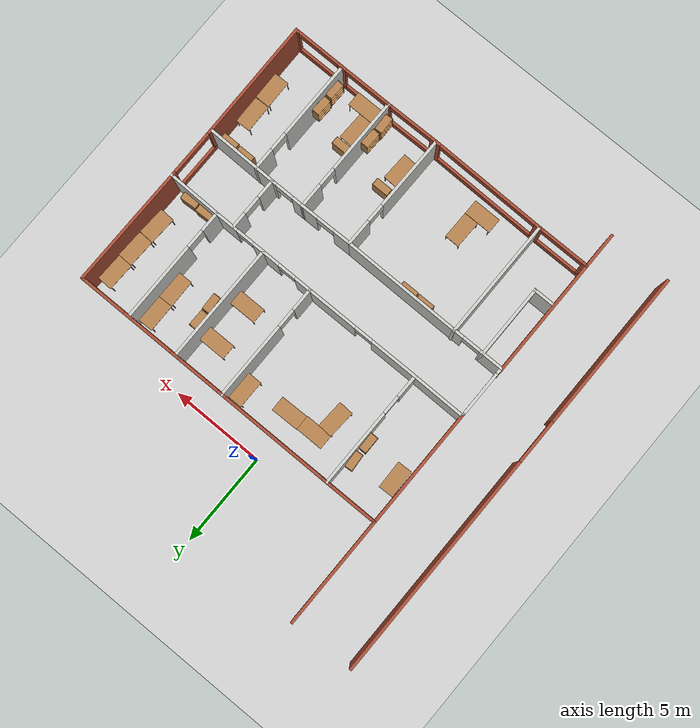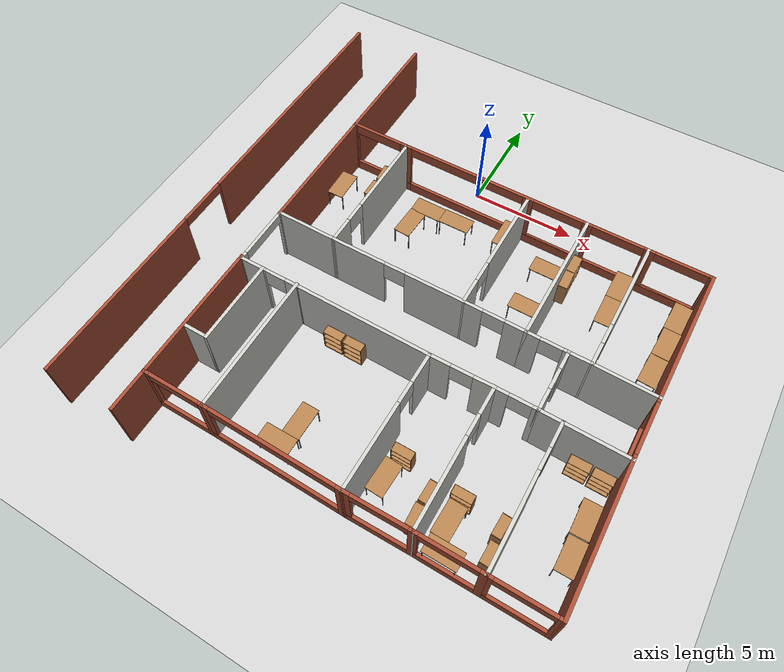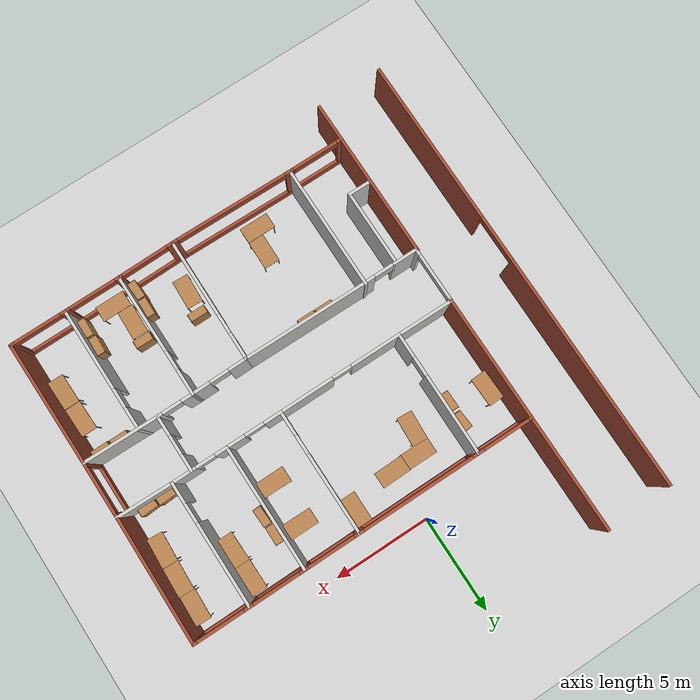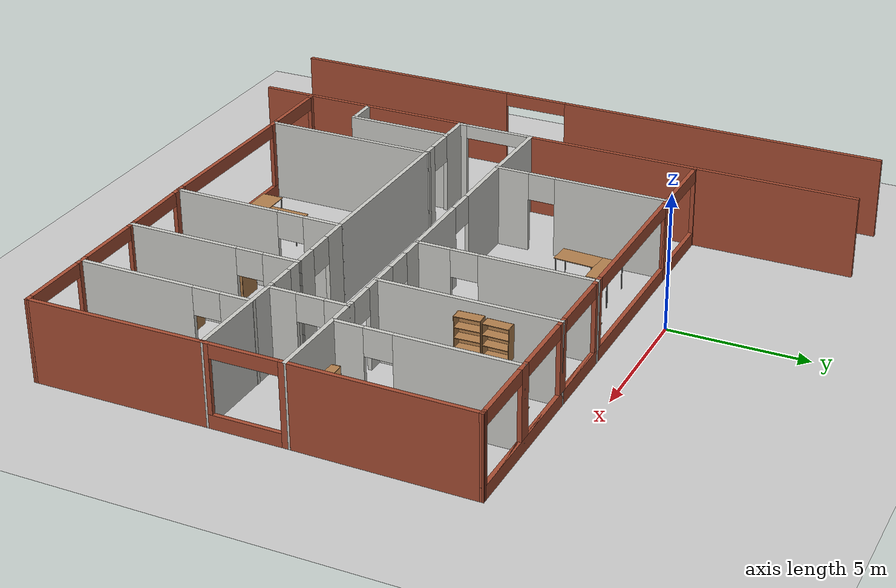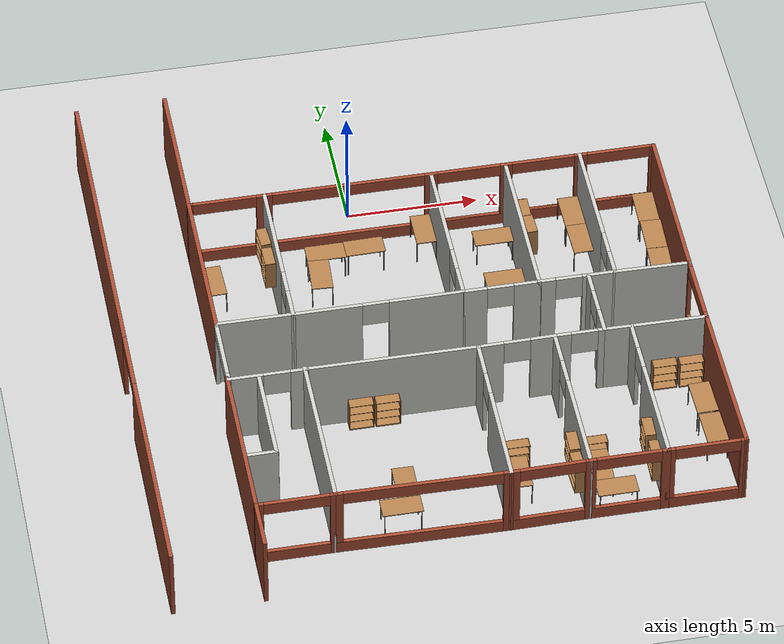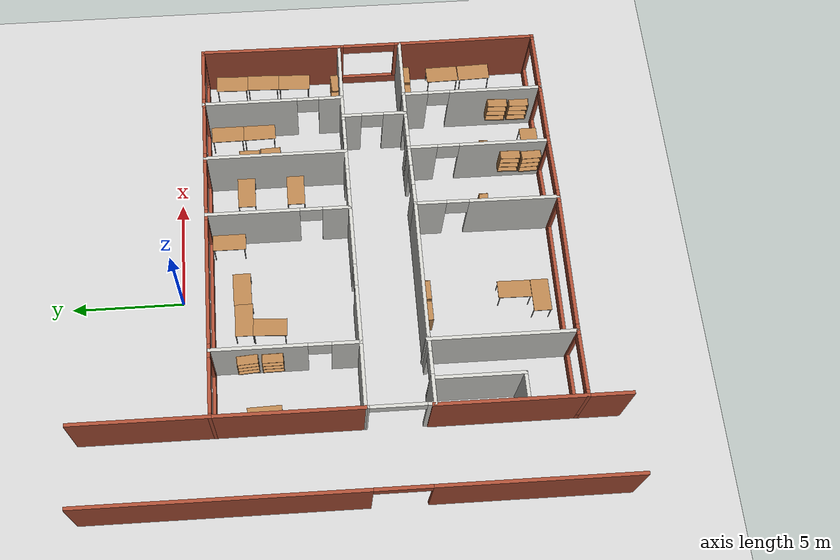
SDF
<sdf version="1.7">
 <world name="default">
  <light name="sun" type="directional">
   <pose>0 0 10 0 -0 0</pose>
   <diffuse>0.8 0.8 0.8 1</diffuse>
   <specular>0.2 0.2 0.2 1</specular>
   <attenuation>
    <range>1000</range>
    <constant>0.9</constant>
    <linear>0.01</linear>
    <quadratic>0.001</quadratic>
   </attenuation>
   <direction>-0.5 0.1 -0.9</direction>
   <spot><inner_angle>0</inner_angle><outer_angle>0</outer_angle><falloff>0</falloff></spot>
  </light>
  <model name="ground_plane">
   <static>1</static>
   <link name="link">
    <collision name="collision">
     <geometry><plane><normal>0 0 1</normal><size>100 100</size></plane></geometry>
     <surface><friction><ode><mu>100</mu><mu2>50</mu2></ode></friction></surface>
    </collision>
    <visual name="visual">
     <cast_shadows>0</cast_shadows>
     <geometry><plane><normal>0 0 1</normal><size>100 100</size></plane></geometry>
     <material>
      <script><uri>file://media/materials/scripts/gazebo.material</uri><name>Gazebo/Grey</name></script>
     </material>
    </visual>
   </link>
  </model>
  <gravity>0 0 -9.8</gravity>
  <magnetic_field>6e-06 2.3e-05 -4.2e-05</magnetic_field>
  <atmosphere type="adiabatic"/>
  <physics type="ode">
   <max_step_size>0.001</max_step_size>
   <real_time_factor>1</real_time_factor>
   <real_time_update_rate>1000</real_time_update_rate>
  </physics>
  <scene><ambient>0.4 0.4 0.4 1</ambient><background>0.7 0.7 0.7 1</background><shadows>1</shadows></scene>
  <spherical_coordinates>
   <surface_model>EARTH_WGS84</surface_model>
   <latitude_deg>0</latitude_deg>
   <longitude_deg>0</longitude_deg>
   <elevation>0</elevation>
   <heading_deg>0</heading_deg>
  </spherical_coordinates>
  <model name="laboratory_world">
   <pose>0.94037 -7.07852 0 0 -0 0</pose>
   <link name="Wall_0">
    <collision name="Wall_0_Collision">
     <geometry><box><size>6.5 0.15 3</size></box></geometry>
     <pose>0 0 1.5 0 -0 0</pose>
    </collision>
    <visual name="Wall_0_Visual">
     <pose>0 0 1.5 0 -0 0</pose>
     <geometry><box><size>6.5 0.15 3</size></box></geometry>
     <material>
      <script><uri>file://media/materials/scripts/gazebo.material</uri><name>Gazebo/Bricks</name></script>
      <ambient>0.760784 0.662745 0.627451 1</ambient>
     </material>
     <meta><layer>0</layer></meta>
    </visual>
    <pose>-7.17678 2.5765 0 0 -0 -1.5708</pose>
   </link>
   <link name="Wall_10">
    <pose>3.44822 -0.5985 0 0 -0 0</pose>
    <visual name="Wall_10_Visual_0">
     <pose>-1.01282 0 1.5 0 -0 0</pose>
     <geometry><box><size>0.974364 0.15 3</size></box></geometry>
     <material>
      <script><uri>file://media/materials/scripts/gazebo.material</uri><name>Gazebo/CeilingTiled</name></script>
      <ambient>0.921569 0.807843 0.615686 1</ambient>
     </material>
     <meta><layer>0</layer></meta>
    </visual>
    <collision name="Wall_10_Collision_0">
     <geometry><box><size>0.974364 0.15 3</size></box></geometry>
     <pose>-1.01282 0 1.5 0 -0 0</pose>
    </collision>
    <visual name="Wall_10_Visual_1">
     <pose>0.987182 0 1.5 0 -0 0</pose>
     <geometry><box><size>1.02564 0.15 3</size></box></geometry>
     <material>
      <script><uri>file://media/materials/scripts/gazebo.material</uri><name>Gazebo/CeilingTiled</name></script>
      <ambient>0.921569 0.807843 0.615686 1</ambient>
     </material>
     <meta><layer>0</layer></meta>
    </visual>
    <collision name="Wall_10_Collision_1">
     <geometry><box><size>1.02564 0.15 3</size></box></geometry>
     <pose>0.987182 0 1.5 0 -0 0</pose>
    </collision>
    <visual name="Wall_10_Visual_2">
     <pose>-0.025636 0 2.5 0 -0 0</pose>
     <geometry><box><size>1 0.15 1</size></box></geometry>
     <material>
      <script><uri>file://media/materials/scripts/gazebo.material</uri><name>Gazebo/CeilingTiled</name></script>
      <ambient>0.921569 0.807843 0.615686 1</ambient>
     </material>
     <meta><layer>0</layer></meta>
    </visual>
    <collision name="Wall_10_Collision_2">
     <geometry><box><size>1 0.15 1</size></box></geometry>
     <pose>-0.025636 0 2.5 0 -0 0</pose>
    </collision>
   </link>
   <link name="Wall_100">
    <collision name="Wall_100_Collision">
     <geometry><box><size>6.5 0.15 3</size></box></geometry>
     <pose>0 0 1.5 0 -0 0</pose>
    </collision>
    <visual name="Wall_100_Visual">
     <pose>0 0 1.5 0 -0 0</pose>
     <geometry><box><size>6.5 0.15 3</size></box></geometry>
     <material>
      <script><uri>file://media/materials/scripts/gazebo.material</uri><name>Gazebo/CeilingTiled</name></script>
      <ambient>0.921569 0.807843 0.615686 1</ambient>
     </material>
     <meta><layer>0</layer></meta>
    </visual>
    <pose>-4.37378 -6.5765 0 0 -0 1.5708</pose>
   </link>
   <link name="Wall_104">
    <pose>-7.17678 -2.0295 0 0 -0 1.5708</pose>
    <visual name="Wall_104_Visual_0">
     <pose>-1.31184 0 1.5 0 -0 0</pose>
     <geometry><box><size>0.388331 0.15 3</size></box></geometry>
     <material>
      <script><uri>file://media/materials/scripts/gazebo.material</uri><name>Gazebo/CeilingTiled</name></script>
      <ambient>0.921569 0.807843 0.615686 1</ambient>
     </material>
     <meta><layer>0</layer></meta>
    </visual>
    <collision name="Wall_104_Collision_0">
     <geometry><box><size>0.388331 0.15 3</size></box></geometry>
     <pose>-1.31184 0 1.5 0 -0 0</pose>
    </collision>
    <visual name="Wall_104_Visual_1">
     <pose>1.39417 0 1.5 0 -0 0</pose>
     <geometry><box><size>0.223669 0.15 3</size></box></geometry>
     <material>
      <script><uri>file://media/materials/scripts/gazebo.material</uri><name>Gazebo/CeilingTiled</name></script>
      <ambient>0.921569 0.807843 0.615686 1</ambient>
     </material>
     <meta><layer>0</layer></meta>
    </visual>
    <collision name="Wall_104_Collision_1">
     <geometry><box><size>0.223669 0.15 3</size></box></geometry>
     <pose>1.39417 0 1.5 0 -0 0</pose>
    </collision>
    <visual name="Wall_104_Visual_2">
     <pose>0.082331 0 2.75 0 -0 0</pose>
     <geometry><box><size>2.4 0.15 0.5</size></box></geometry>
     <material>
      <script><uri>file://media/materials/scripts/gazebo.material</uri><name>Gazebo/CeilingTiled</name></script>
      <ambient>0.921569 0.807843 0.615686 1</ambient>
     </material>
     <meta><layer>0</layer></meta>
    </visual>
    <collision name="Wall_104_Collision_2">
     <geometry><box><size>2.4 0.15 0.5</size></box></geometry>
     <pose>0.082331 0 2.75 0 -0 0</pose>
    </collision>
   </link>
   <link name="Wall_106">
    <collision name="Wall_106_Collision">
     <geometry><box><size>1.2 0.15 3</size></box></geometry>
     <pose>0 0 1.5 0 -0 0</pose>
    </collision>
    <visual name="Wall_106_Visual">
     <pose>0 0 1.5 0 -0 0</pose>
     <geometry><box><size>1.2 0.15 3</size></box></geometry>
     <material>
      <script><uri>file://media/materials/scripts/gazebo.material</uri><name>Gazebo/CeilingTiled</name></script>
      <ambient>0.921569 0.807843 0.615686 1</ambient>
     </material>
     <meta><layer>0</layer></meta>
    </visual>
    <pose>-6.60478 -7.3105 0 0 -0 0</pose>
   </link>
   <link name="Wall_108">
    <collision name="Wall_108_Collision">
     <geometry><box><size>4 0.15 3</size></box></geometry>
     <pose>0 0 1.5 0 -0 0</pose>
    </collision>
    <visual name="Wall_108_Visual">
     <pose>0 0 1.5 0 -0 0</pose>
     <geometry><box><size>4 0.15 3</size></box></geometry>
     <material>
      <script><uri>file://media/materials/scripts/gazebo.material</uri><name>Gazebo/CeilingTiled</name></script>
      <ambient>0.921569 0.807843 0.615686 1</ambient>
     </material>
     <meta><layer>0</layer></meta>
    </visual>
    <pose>-6.07978 -5.3855 0 0 -0 1.5708</pose>
   </link>
   <link name="Wall_11">
    <collision name="Wall_11_Collision">
     <geometry><box><size>6.5 0.15 3</size></box></geometry>
     <pose>0 0 1.5 0 -0 0</pose>
    </collision>
    <visual name="Wall_11_Visual">
     <pose>0 0 1.5 0 -0 0</pose>
     <geometry><box><size>6.5 0.15 3</size></box></geometry>
     <material>
      <script><uri>file://media/materials/scripts/gazebo.material</uri><name>Gazebo/CeilingTiled</name></script>
      <ambient>0.921569 0.807843 0.615686 1</ambient>
     </material>
     <meta><layer>0</layer></meta>
    </visual>
    <pose>4.87322 2.5765 0 0 -0 1.5708</pose>
   </link>
   <link name="Wall_112">
    <pose>-5.79878 -9.7515 0 0 -0 3.14159</pose>
    <visual name="Wall_112_Visual_0">
     <pose>-1.36527 0 1.5 0 -0 0</pose>
     <geometry><box><size>0.269459 0.15 3</size></box></geometry>
     <material>
      <script><uri>file://media/materials/scripts/gazebo.material</uri><name>Gazebo/Bricks</name></script>
      <ambient>0.760784 0.662745 0.627451 1</ambient>
     </material>
     <meta><layer>0</layer></meta>
    </visual>
    <collision name="Wall_112_Collision_0">
     <geometry><box><size>0.269459 0.15 3</size></box></geometry>
     <pose>-1.36527 0 1.5 0 -0 0</pose>
    </collision>
    <visual name="Wall_112_Visual_1">
     <pose>0.134729 0 0.25 0 -0 0</pose>
     <geometry><box><size>2.73054 0.15 0.5</size></box></geometry>
     <material>
      <script><uri>file://media/materials/scripts/gazebo.material</uri><name>Gazebo/Bricks</name></script>
      <ambient>0.760784 0.662745 0.627451 1</ambient>
     </material>
     <meta><layer>0</layer></meta>
    </visual>
    <collision name="Wall_112_Collision_1">
     <geometry><box><size>2.73054 0.15 0.5</size></box></geometry>
     <pose>0.134729 0 0.25 0 -0 0</pose>
    </collision>
    <visual name="Wall_112_Visual_2">
     <pose>1.33473 0 1.75 0 -0 0</pose>
     <geometry><box><size>0.330541 0.15 2.5</size></box></geometry>
     <material>
      <script><uri>file://media/materials/scripts/gazebo.material</uri><name>Gazebo/Bricks</name></script>
      <ambient>0.760784 0.662745 0.627451 1</ambient>
     </material>
     <meta><layer>0</layer></meta>
    </visual>
    <collision name="Wall_112_Collision_2">
     <geometry><box><size>0.330541 0.15 2.5</size></box></geometry>
     <pose>1.33473 0 1.75 0 -0 0</pose>
    </collision>
    <visual name="Wall_112_Visual_3">
     <pose>-0.030541 0 2.75 0 -0 0</pose>
     <geometry><box><size>2.4 0.15 0.5</size></box></geometry>
     <material>
      <script><uri>file://media/materials/scripts/gazebo.material</uri><name>Gazebo/Bricks</name></script>
      <ambient>0.760784 0.662745 0.627451 1</ambient>
     </material>
     <meta><layer>0</layer></meta>
    </visual>
    <collision name="Wall_112_Collision_3">
     <geometry><box><size>2.4 0.15 0.5</size></box></geometry>
     <pose>-0.030541 0 2.75 0 -0 0</pose>
    </collision>
   </link>
   <link name="Wall_114">
    <collision name="Wall_114_Collision">
     <geometry><box><size>6.5 0.15 3</size></box></geometry>
     <pose>0 0 1.5 0 -0 0</pose>
    </collision>
    <visual name="Wall_114_Visual">
     <pose>0 0 1.5 0 -0 0</pose>
     <geometry><box><size>6.5 0.15 3</size></box></geometry>
     <material>
      <script><uri>file://media/materials/scripts/gazebo.material</uri><name>Gazebo/Bricks</name></script>
      <ambient>0.760784 0.662745 0.627451 1</ambient>
     </material>
     <meta><layer>0</layer></meta>
    </visual>
    <pose>-7.22378 -6.5765 0 0 -0 1.5708</pose>
   </link>
   <link name="Wall_116">
    <collision name="Wall_116_Collision">
     <geometry><box><size>6 0.15 3</size></box></geometry>
     <pose>0 0 1.5 0 -0 0</pose>
    </collision>
    <visual name="Wall_116_Visual">
     <pose>0 0 1.5 0 -0 0</pose>
     <geometry><box><size>6 0.15 3</size></box></geometry>
     <material>
      <script><uri>file://media/materials/scripts/gazebo.material</uri><name>Gazebo/Bricks</name></script>
      <ambient>0.760784 0.662745 0.627451 1</ambient>
     </material>
     <meta><layer>0</layer></meta>
    </visual>
    <pose>-7.17678 8.6765 0 0 -0 1.5708</pose>
   </link>
   <link name="Wall_118">
    <collision name="Wall_118_Collision">
     <geometry><box><size>2 0.15 3</size></box></geometry>
     <pose>0 0 1.5 0 -0 0</pose>
    </collision>
    <visual name="Wall_118_Visual">
     <pose>0 0 1.5 0 -0 0</pose>
     <geometry><box><size>2 0.15 3</size></box></geometry>
     <material>
      <script><uri>file://media/materials/scripts/gazebo.material</uri><name>Gazebo/Bricks</name></script>
      <ambient>0.760784 0.662745 0.627451 1</ambient>
     </material>
     <meta><layer>0</layer></meta>
    </visual>
    <pose>-7.22378 -10.6765 0 0 -0 -1.5708</pose>
   </link>
   <link name="Wall_123">
    <pose>-10.5738 -0.0515 0 0 -0 1.5708</pose>
    <visual name="Wall_123_Visual_0">
     <pose>-7.31381 0 1.5 0 -0 0</pose>
     <geometry><box><size>8.62238 0.15 3</size></box></geometry>
     <material>
      <script><uri>file://media/materials/scripts/gazebo.material</uri><name>Gazebo/Bricks</name></script>
      <ambient>0.921569 0.807843 0.615686 1</ambient>
     </material>
     <meta><layer>0</layer></meta>
    </visual>
    <collision name="Wall_123_Collision_0">
     <geometry><box><size>8.62238 0.15 3</size></box></geometry>
     <pose>-7.31381 0 1.5 0 -0 0</pose>
    </collision>
    <visual name="Wall_123_Visual_1">
     <pose>5.51119 0 1.5 0 -0 0</pose>
     <geometry><box><size>12.2276 0.15 3</size></box></geometry>
     <material>
      <script><uri>file://media/materials/scripts/gazebo.material</uri><name>Gazebo/Bricks</name></script>
      <ambient>0.921569 0.807843 0.615686 1</ambient>
     </material>
     <meta><layer>0</layer></meta>
    </visual>
    <collision name="Wall_123_Collision_1">
     <geometry><box><size>12.2276 0.15 3</size></box></geometry>
     <pose>5.51119 0 1.5 0 -0 0</pose>
    </collision>
    <visual name="Wall_123_Visual_2">
     <pose>-1.80262 0 2.75 0 -0 0</pose>
     <geometry><box><size>2.4 0.15 0.5</size></box></geometry>
     <material>
      <script><uri>file://media/materials/scripts/gazebo.material</uri><name>Gazebo/Bricks</name></script>
      <ambient>0.921569 0.807843 0.615686 1</ambient>
     </material>
     <meta><layer>0</layer></meta>
    </visual>
    <collision name="Wall_123_Collision_2">
     <geometry><box><size>2.4 0.15 0.5</size></box></geometry>
     <pose>-1.80262 0 2.75 0 -0 0</pose>
    </collision>
   </link>
   <link name="Wall_13">
    <pose>6.29822 -0.5985 0 0 -0 0</pose>
    <visual name="Wall_13_Visual_0">
     <pose>-1.1523 0 1.5 0 -0 0</pose>
     <geometry><box><size>0.695403 0.15 3</size></box></geometry>
     <material>
      <script><uri>file://media/materials/scripts/gazebo.material</uri><name>Gazebo/CeilingTiled</name></script>
      <ambient>0.921569 0.807843 0.615686 1</ambient>
     </material>
     <meta><layer>0</layer></meta>
    </visual>
    <collision name="Wall_13_Collision_0">
     <geometry><box><size>0.695403 0.15 3</size></box></geometry>
     <pose>-1.1523 0 1.5 0 -0 0</pose>
    </collision>
    <visual name="Wall_13_Visual_1">
     <pose>0.847702 0 1.5 0 -0 0</pose>
     <geometry><box><size>1.3046 0.15 3</size></box></geometry>
     <material>
      <script><uri>file://media/materials/scripts/gazebo.material</uri><name>Gazebo/CeilingTiled</name></script>
      <ambient>0.921569 0.807843 0.615686 1</ambient>
     </material>
     <meta><layer>0</layer></meta>
    </visual>
    <collision name="Wall_13_Collision_1">
     <geometry><box><size>1.3046 0.15 3</size></box></geometry>
     <pose>0.847702 0 1.5 0 -0 0</pose>
    </collision>
    <visual name="Wall_13_Visual_2">
     <pose>-0.304597 0 2.5 0 -0 0</pose>
     <geometry><box><size>1 0.15 1</size></box></geometry>
     <material>
      <script><uri>file://media/materials/scripts/gazebo.material</uri><name>Gazebo/CeilingTiled</name></script>
      <ambient>0.921569 0.807843 0.615686 1</ambient>
     </material>
     <meta><layer>0</layer></meta>
    </visual>
    <collision name="Wall_13_Collision_2">
     <geometry><box><size>1 0.15 1</size></box></geometry>
     <pose>-0.304597 0 2.5 0 -0 0</pose>
    </collision>
   </link>
   <link name="Wall_14">
    <pose>7.72322 2.5765 0 0 -0 1.5708</pose>
    <visual name="Wall_14_Visual_0">
     <pose>-2.67901 0 1.5 0 -0 0</pose>
     <geometry><box><size>1.14198 0.15 3</size></box></geometry>
     <material>
      <script><uri>file://media/materials/scripts/gazebo.material</uri><name>Gazebo/CeilingTiled</name></script>
      <ambient>0.921569 0.807843 0.615686 1</ambient>
     </material>
     <meta><layer>0</layer></meta>
    </visual>
    <collision name="Wall_14_Collision_0">
     <geometry><box><size>1.14198 0.15 3</size></box></geometry>
     <pose>-2.67901 0 1.5 0 -0 0</pose>
    </collision>
    <visual name="Wall_14_Visual_1">
     <pose>1.07099 0 1.5 0 -0 0</pose>
     <geometry><box><size>4.35802 0.15 3</size></box></geometry>
     <material>
      <script><uri>file://media/materials/scripts/gazebo.material</uri><name>Gazebo/CeilingTiled</name></script>
      <ambient>0.921569 0.807843 0.615686 1</ambient>
     </material>
     <meta><layer>0</layer></meta>
    </visual>
    <collision name="Wall_14_Collision_1">
     <geometry><box><size>4.35802 0.15 3</size></box></geometry>
     <pose>1.07099 0 1.5 0 -0 0</pose>
    </collision>
    <visual name="Wall_14_Visual_2">
     <pose>-1.60802 0 2.5 0 -0 0</pose>
     <geometry><box><size>1 0.15 1</size></box></geometry>
     <material>
      <script><uri>file://media/materials/scripts/gazebo.material</uri><name>Gazebo/CeilingTiled</name></script>
      <ambient>0.921569 0.807843 0.615686 1</ambient>
     </material>
     <meta><layer>0</layer></meta>
    </visual>
    <collision name="Wall_14_Collision_2">
     <geometry><box><size>1 0.15 1</size></box></geometry>
     <pose>-1.60802 0 2.5 0 -0 0</pose>
    </collision>
   </link>
   <link name="Wall_16">
    <collision name="Wall_16_Collision">
     <geometry><box><size>2.95339 0.15 3</size></box></geometry>
     <pose>0 0 1.5 0 -0 0</pose>
    </collision>
    <visual name="Wall_16_Visual">
     <pose>0 0 1.5 0 -0 0</pose>
     <geometry><box><size>2.95339 0.15 3</size></box></geometry>
     <material>
      <script><uri>file://media/materials/scripts/gazebo.material</uri><name>Gazebo/CeilingTiled</name></script>
      <ambient>0.921569 0.807843 0.615686 1</ambient>
     </material>
     <meta><layer>0</layer></meta>
    </visual>
    <pose>9.12472 -0.622 0 0 -0 -0.016766</pose>
   </link>
   <link name="Wall_17">
    <collision name="Wall_17_Collision">
     <geometry><box><size>6.54717 0.15 3</size></box></geometry>
     <pose>0 0 1.5 0 -0 0</pose>
    </collision>
    <visual name="Wall_17_Visual">
     <pose>0 0 1.5 0 -0 0</pose>
     <geometry><box><size>6.54717 0.15 3</size></box></geometry>
     <material>
      <script><uri>file://media/materials/scripts/gazebo.material</uri><name>Gazebo/Bricks</name></script>
      <ambient>0.760784 0.662745 0.627451 1</ambient>
     </material>
     <meta><layer>0</layer></meta>
    </visual>
    <pose>10.5497 2.553 0 0 -0 1.56345</pose>
   </link>
   <link name="Wall_19">
    <pose>1.69822 5.7515 0 0 -0 0</pose>
    <visual name="Wall_19_Visual_0">
     <pose>-8.8394 0 1.5 0 -0 0</pose>
     <geometry><box><size>0.221205 0.15 3</size></box></geometry>
     <material>
      <script><uri>file://media/materials/scripts/gazebo.material</uri><name>Gazebo/Bricks</name></script>
      <ambient>0.760784 0.662745 0.627451 1</ambient>
     </material>
     <meta><layer>0</layer></meta>
    </visual>
    <collision name="Wall_19_Collision_0">
     <geometry><box><size>0.221205 0.15 3</size></box></geometry>
     <pose>-8.8394 0 1.5 0 -0 0</pose>
    </collision>
    <visual name="Wall_19_Visual_1">
     <pose>-7.22592 0 0.25 0 -0 0</pose>
     <geometry><box><size>3.00574 0.15 0.5</size></box></geometry>
     <material>
      <script><uri>file://media/materials/scripts/gazebo.material</uri><name>Gazebo/Bricks</name></script>
      <ambient>0.760784 0.662745 0.627451 1</ambient>
     </material>
     <meta><layer>0</layer></meta>
    </visual>
    <collision name="Wall_19_Collision_1">
     <geometry><box><size>3.00574 0.15 0.5</size></box></geometry>
     <pose>-7.22592 0 0.25 0 -0 0</pose>
    </collision>
    <visual name="Wall_19_Visual_2">
     <pose>-5.72305 0 1.5 0 -0 0</pose>
     <geometry><box><size>0 0.15 3</size></box></geometry>
     <material>
      <script><uri>file://media/materials/scripts/gazebo.material</uri><name>Gazebo/Bricks</name></script>
      <ambient>0.760784 0.662745 0.627451 1</ambient>
     </material>
     <meta><layer>0</layer></meta>
    </visual>
    <collision name="Wall_19_Collision_2">
     <geometry><box><size>0 0.15 3</size></box></geometry>
     <pose>-5.72305 0 1.5 0 -0 0</pose>
    </collision>
    <visual name="Wall_19_Visual_3">
     <pose>1.61347 0 0.25 0 -0 0</pose>
     <geometry><box><size>14.6731 0.15 0.5</size></box></geometry>
     <material>
      <script><uri>file://media/materials/scripts/gazebo.material</uri><name>Gazebo/Bricks</name></script>
      <ambient>0.760784 0.662745 0.627451 1</ambient>
     </material>
     <meta><layer>0</layer></meta>
    </visual>
    <collision name="Wall_19_Collision_3">
     <geometry><box><size>14.6731 0.15 0.5</size></box></geometry>
     <pose>1.61347 0 0.25 0 -0 0</pose>
    </collision>
    <visual name="Wall_19_Visual_4">
     <pose>0.326891 0 1.75 0 -0 0</pose>
     <geometry><box><size>0.499886 0.15 2.5</size></box></geometry>
     <material>
      <script><uri>file://media/materials/scripts/gazebo.material</uri><name>Gazebo/Bricks</name></script>
      <ambient>0.760784 0.662745 0.627451 1</ambient>
     </material>
     <meta><layer>0</layer></meta>
    </visual>
    <collision name="Wall_19_Collision_4">
     <geometry><box><size>0.499886 0.15 2.5</size></box></geometry>
     <pose>0.326891 0 1.75 0 -0 0</pose>
    </collision>
    <visual name="Wall_19_Visual_5">
     <pose>3.20242 0 1.75 0 -0 0</pose>
     <geometry><box><size>0.451166 0.15 2.5</size></box></geometry>
     <material>
      <script><uri>file://media/materials/scripts/gazebo.material</uri><name>Gazebo/Bricks</name></script>
      <ambient>0.760784 0.662745 0.627451 1</ambient>
     </material>
     <meta><layer>0</layer></meta>
    </visual>
    <collision name="Wall_19_Collision_5">
     <geometry><box><size>0.451166 0.15 2.5</size></box></geometry>
     <pose>3.20242 0 1.75 0 -0 0</pose>
    </collision>
    <visual name="Wall_19_Visual_6">
     <pose>6.07079 0 1.75 0 -0 0</pose>
     <geometry><box><size>0.485575 0.15 2.5</size></box></geometry>
     <material>
      <script><uri>file://media/materials/scripts/gazebo.material</uri><name>Gazebo/Bricks</name></script>
      <ambient>0.760784 0.662745 0.627451 1</ambient>
     </material>
     <meta><layer>0</layer></meta>
    </visual>
    <collision name="Wall_19_Collision_6">
     <geometry><box><size>0.485575 0.15 2.5</size></box></geometry>
     <pose>6.07079 0 1.75 0 -0 0</pose>
    </collision>
    <visual name="Wall_19_Visual_7">
     <pose>8.83179 0 1.75 0 -0 0</pose>
     <geometry><box><size>0.236425 0.15 2.5</size></box></geometry>
     <material>
      <script><uri>file://media/materials/scripts/gazebo.material</uri><name>Gazebo/Bricks</name></script>
      <ambient>0.760784 0.662745 0.627451 1</ambient>
     </material>
     <meta><layer>0</layer></meta>
    </visual>
    <collision name="Wall_19_Collision_7">
     <geometry><box><size>0.236425 0.15 2.5</size></box></geometry>
     <pose>8.83179 0 1.75 0 -0 0</pose>
    </collision>
    <visual name="Wall_19_Visual_8">
     <pose>1.77683 0 0.5 0 -0 0</pose>
     <geometry><box><size>2.4 0.15 0</size></box></geometry>
     <material>
      <script><uri>file://media/materials/scripts/gazebo.material</uri><name>Gazebo/Bricks</name></script>
      <ambient>0.760784 0.662745 0.627451 1</ambient>
     </material>
     <meta><layer>0</layer></meta>
    </visual>
    <collision name="Wall_19_Collision_8">
     <geometry><box><size>2.4 0.15 0</size></box></geometry>
     <pose>1.77683 0 0.5 0 -0 0</pose>
    </collision>
    <visual name="Wall_19_Visual_9">
     <pose>4.628 0 0.5 0 -0 0</pose>
     <geometry><box><size>2.4 0.15 0</size></box></geometry>
     <material>
      <script><uri>file://media/materials/scripts/gazebo.material</uri><name>Gazebo/Bricks</name></script>
      <ambient>0.760784 0.662745 0.627451 1</ambient>
     </material>
     <meta><layer>0</layer></meta>
    </visual>
    <collision name="Wall_19_Collision_9">
     <geometry><box><size>2.4 0.15 0</size></box></geometry>
     <pose>4.628 0 0.5 0 -0 0</pose>
    </collision>
    <visual name="Wall_19_Visual_10">
     <pose>7.51358 0 0.5 0 -0 0</pose>
     <geometry><box><size>2.4 0.15 0</size></box></geometry>
     <material>
      <script><uri>file://media/materials/scripts/gazebo.material</uri><name>Gazebo/Bricks</name></script>
      <ambient>0.760784 0.662745 0.627451 1</ambient>
     </material>
     <meta><layer>0</layer></meta>
    </visual>
    <collision name="Wall_19_Collision_10">
     <geometry><box><size>2.4 0.15 0</size></box></geometry>
     <pose>7.51358 0 0.5 0 -0 0</pose>
    </collision>
    <visual name="Wall_19_Visual_11">
     <pose>-6.02592 0 1.75 0 -0 0</pose>
     <geometry><box><size>0.605742 0.15 2.5</size></box></geometry>
     <material>
      <script><uri>file://media/materials/scripts/gazebo.material</uri><name>Gazebo/Bricks</name></script>
      <ambient>0.760784 0.662745 0.627451 1</ambient>
     </material>
     <meta><layer>0</layer></meta>
    </visual>
    <collision name="Wall_19_Collision_11">
     <geometry><box><size>0.605742 0.15 2.5</size></box></geometry>
     <pose>-6.02592 0 1.75 0 -0 0</pose>
    </collision>
    <visual name="Wall_19_Visual_12">
     <pose>-6.02592 0 1.75 0 -0 0</pose>
     <geometry><box><size>0.605742 0.15 2.5</size></box></geometry>
     <material>
      <script><uri>file://media/materials/scripts/gazebo.material</uri><name>Gazebo/Bricks</name></script>
      <ambient>0.760784 0.662745 0.627451 1</ambient>
     </material>
     <meta><layer>0</layer></meta>
    </visual>
    <collision name="Wall_19_Collision_12">
     <geometry><box><size>0.605742 0.15 2.5</size></box></geometry>
     <pose>-6.02592 0 1.75 0 -0 0</pose>
    </collision>
    <visual name="Wall_19_Visual_13">
     <pose>-2.82305 0 2.75 0 -0 0</pose>
     <geometry><box><size>5.8 0.15 0.5</size></box></geometry>
     <material>
      <script><uri>file://media/materials/scripts/gazebo.material</uri><name>Gazebo/Bricks</name></script>
      <ambient>0.760784 0.662745 0.627451 1</ambient>
     </material>
     <meta><layer>0</layer></meta>
    </visual>
    <collision name="Wall_19_Collision_13">
     <geometry><box><size>5.8 0.15 0.5</size></box></geometry>
     <pose>-2.82305 0 2.75 0 -0 0</pose>
    </collision>
    <visual name="Wall_19_Visual_14">
     <pose>-7.52879 0 2.75 0 -0 0</pose>
     <geometry><box><size>2.4 0.15 0.5</size></box></geometry>
     <material>
      <script><uri>file://media/materials/scripts/gazebo.material</uri><name>Gazebo/Bricks</name></script>
      <ambient>0.760784 0.662745 0.627451 1</ambient>
     </material>
     <meta><layer>0</layer></meta>
    </visual>
    <collision name="Wall_19_Collision_14">
     <geometry><box><size>2.4 0.15 0.5</size></box></geometry>
     <pose>-7.52879 0 2.75 0 -0 0</pose>
    </collision>
    <visual name="Wall_19_Visual_15">
     <pose>1.77683 0 2.75 0 -0 0</pose>
     <geometry><box><size>2.4 0.15 0.5</size></box></geometry>
     <material>
      <script><uri>file://media/materials/scripts/gazebo.material</uri><name>Gazebo/Bricks</name></script>
      <ambient>0.760784 0.662745 0.627451 1</ambient>
     </material>
     <meta><layer>0</layer></meta>
    </visual>
    <collision name="Wall_19_Collision_15">
     <geometry><box><size>2.4 0.15 0.5</size></box></geometry>
     <pose>1.77683 0 2.75 0 -0 0</pose>
    </collision>
    <visual name="Wall_19_Visual_16">
     <pose>4.628 0 2.75 0 -0 0</pose>
     <geometry><box><size>2.4 0.15 0.5</size></box></geometry>
     <material>
      <script><uri>file://media/materials/scripts/gazebo.material</uri><name>Gazebo/Bricks</name></script>
      <ambient>0.760784 0.662745 0.627451 1</ambient>
     </material>
     <meta><layer>0</layer></meta>
    </visual>
    <collision name="Wall_19_Collision_16">
     <geometry><box><size>2.4 0.15 0.5</size></box></geometry>
     <pose>4.628 0 2.75 0 -0 0</pose>
    </collision>
    <visual name="Wall_19_Visual_17">
     <pose>7.51358 0 2.75 0 -0 0</pose>
     <geometry><box><size>2.4 0.15 0.5</size></box></geometry>
     <material>
      <script><uri>file://media/materials/scripts/gazebo.material</uri><name>Gazebo/Bricks</name></script>
      <ambient>0.760784 0.662745 0.627451 1</ambient>
     </material>
     <meta><layer>0</layer></meta>
    </visual>
    <collision name="Wall_19_Collision_17">
     <geometry><box><size>2.4 0.15 0.5</size></box></geometry>
     <pose>7.51358 0 2.75 0 -0 0</pose>
    </collision>
   </link>
   <link name="Wall_21">
    <pose>10.5262 -2.0705 0 0 -0 -1.5708</pose>
    <visual name="Wall_21_Visual_0">
     <pose>-1.35631 0 1.5 0 -0 0</pose>
     <geometry><box><size>0.287384 0.15 3</size></box></geometry>
     <material>
      <script><uri>file://media/materials/scripts/gazebo.material</uri><name>Gazebo/Bricks</name></script>
      <ambient>0.760784 0.662745 0.627451 1</ambient>
     </material>
     <meta><layer>0</layer></meta>
    </visual>
    <collision name="Wall_21_Collision_0">
     <geometry><box><size>0.287384 0.15 3</size></box></geometry>
     <pose>-1.35631 0 1.5 0 -0 0</pose>
    </collision>
    <visual name="Wall_21_Visual_1">
     <pose>0.143692 0 0.25 0 -0 0</pose>
     <geometry><box><size>2.71262 0.15 0.5</size></box></geometry>
     <material>
      <script><uri>file://media/materials/scripts/gazebo.material</uri><name>Gazebo/Bricks</name></script>
      <ambient>0.760784 0.662745 0.627451 1</ambient>
     </material>
     <meta><layer>0</layer></meta>
    </visual>
    <collision name="Wall_21_Collision_1">
     <geometry><box><size>2.71262 0.15 0.5</size></box></geometry>
     <pose>0.143692 0 0.25 0 -0 0</pose>
    </collision>
    <visual name="Wall_21_Visual_2">
     <pose>1.34369 0 1.75 0 -0 0</pose>
     <geometry><box><size>0.312616 0.15 2.5</size></box></geometry>
     <material>
      <script><uri>file://media/materials/scripts/gazebo.material</uri><name>Gazebo/Bricks</name></script>
      <ambient>0.760784 0.662745 0.627451 1</ambient>
     </material>
     <meta><layer>0</layer></meta>
    </visual>
    <collision name="Wall_21_Collision_2">
     <geometry><box><size>0.312616 0.15 2.5</size></box></geometry>
     <pose>1.34369 0 1.75 0 -0 0</pose>
    </collision>
    <visual name="Wall_21_Visual_3">
     <pose>-0.012616 0 2.75 0 -0 0</pose>
     <geometry><box><size>2.4 0.15 0.5</size></box></geometry>
     <material>
      <script><uri>file://media/materials/scripts/gazebo.material</uri><name>Gazebo/Bricks</name></script>
      <ambient>0.760784 0.662745 0.627451 1</ambient>
     </material>
     <meta><layer>0</layer></meta>
    </visual>
    <collision name="Wall_21_Collision_3">
     <geometry><box><size>2.4 0.15 0.5</size></box></geometry>
     <pose>-0.012616 0 2.75 0 -0 0</pose>
    </collision>
   </link>
   <link name="Wall_22">
    <collision name="Wall_22_Collision">
     <geometry><box><size>3.95329 0.15 3</size></box></geometry>
     <pose>0 0 1.5 0 -0 0</pose>
    </collision>
    <visual name="Wall_22_Visual">
     <pose>0 0 1.5 0 -0 0</pose>
     <geometry><box><size>3.95329 0.15 3</size></box></geometry>
     <material>
      <script><uri>file://media/materials/scripts/gazebo.material</uri><name>Gazebo/CeilingTiled</name></script>
      <ambient>0.921569 0.807843 0.615686 1</ambient>
     </material>
     <meta><layer>0</layer></meta>
    </visual>
    <pose>8.62472 -3.472 0 0 -0 3.12923</pose>
   </link>
   <link name="Wall_23">
    <pose>6.72322 -2.0235 0 0 -0 1.5708</pose>
    <visual name="Wall_23_Visual_0">
     <pose>-0.956509 0 1.5 0 -0 0</pose>
     <geometry><box><size>1.08698 0.15 3</size></box></geometry>
     <material>
      <script><uri>file://media/materials/scripts/gazebo.material</uri><name>Gazebo/CeilingTiled</name></script>
      <ambient>0.921569 0.807843 0.615686 1</ambient>
     </material>
     <meta><layer>0</layer></meta>
    </visual>
    <collision name="Wall_23_Collision_0">
     <geometry><box><size>1.08698 0.15 3</size></box></geometry>
     <pose>-0.956509 0 1.5 0 -0 0</pose>
    </collision>
    <visual name="Wall_23_Visual_1">
     <pose>1.04349 0 1.5 0 -0 0</pose>
     <geometry><box><size>0.913017 0.15 3</size></box></geometry>
     <material>
      <script><uri>file://media/materials/scripts/gazebo.material</uri><name>Gazebo/CeilingTiled</name></script>
      <ambient>0.921569 0.807843 0.615686 1</ambient>
     </material>
     <meta><layer>0</layer></meta>
    </visual>
    <collision name="Wall_23_Collision_1">
     <geometry><box><size>0.913017 0.15 3</size></box></geometry>
     <pose>1.04349 0 1.5 0 -0 0</pose>
    </collision>
    <visual name="Wall_23_Visual_2">
     <pose>0.086983 0 2.5 0 -0 0</pose>
     <geometry><box><size>1 0.15 1</size></box></geometry>
     <material>
      <script><uri>file://media/materials/scripts/gazebo.material</uri><name>Gazebo/CeilingTiled</name></script>
      <ambient>0.921569 0.807843 0.615686 1</ambient>
     </material>
     <meta><layer>0</layer></meta>
    </visual>
    <collision name="Wall_23_Collision_2">
     <geometry><box><size>1 0.15 1</size></box></geometry>
     <pose>0.086983 0 2.5 0 -0 0</pose>
    </collision>
   </link>
   <link name="Wall_26">
    <collision name="Wall_26_Collision">
     <geometry><box><size>6.45317 0.15 3</size></box></geometry>
     <pose>0 0 1.5 0 -0 0</pose>
    </collision>
    <visual name="Wall_26_Visual">
     <pose>0 0 1.5 0 -0 0</pose>
     <geometry><box><size>6.45317 0.15 3</size></box></geometry>
     <material>
      <script><uri>file://media/materials/scripts/gazebo.material</uri><name>Gazebo/Bricks</name></script>
      <ambient>0.760784 0.662745 0.627451 1</ambient>
     </material>
     <meta><layer>0</layer></meta>
    </visual>
    <pose>10.5497 -6.647 0 0 -0 -1.56334</pose>
   </link>
   <link name="Wall_29">
    <pose>9.14822 -9.7985 0 0 -0 3.14159</pose>
    <visual name="Wall_29_Visual_0">
     <pose>-1.36291 0 1.5 0 -0 0</pose>
     <geometry><box><size>0.274173 0.15 3</size></box></geometry>
     <material>
      <script><uri>file://media/materials/scripts/gazebo.material</uri><name>Gazebo/Bricks</name></script>
      <ambient>0.760784 0.662745 0.627451 1</ambient>
     </material>
     <meta><layer>0</layer></meta>
    </visual>
    <collision name="Wall_29_Collision_0">
     <geometry><box><size>0.274173 0.15 3</size></box></geometry>
     <pose>-1.36291 0 1.5 0 -0 0</pose>
    </collision>
    <visual name="Wall_29_Visual_1">
     <pose>0.137086 0 0.25 0 -0 0</pose>
     <geometry><box><size>2.72583 0.15 0.5</size></box></geometry>
     <material>
      <script><uri>file://media/materials/scripts/gazebo.material</uri><name>Gazebo/Bricks</name></script>
      <ambient>0.760784 0.662745 0.627451 1</ambient>
     </material>
     <meta><layer>0</layer></meta>
    </visual>
    <collision name="Wall_29_Collision_1">
     <geometry><box><size>2.72583 0.15 0.5</size></box></geometry>
     <pose>0.137086 0 0.25 0 -0 0</pose>
    </collision>
    <visual name="Wall_29_Visual_2">
     <pose>1.33709 0 1.75 0 -0 0</pose>
     <geometry><box><size>0.325827 0.15 2.5</size></box></geometry>
     <material>
      <script><uri>file://media/materials/scripts/gazebo.material</uri><name>Gazebo/Bricks</name></script>
      <ambient>0.760784 0.662745 0.627451 1</ambient>
     </material>
     <meta><layer>0</layer></meta>
    </visual>
    <collision name="Wall_29_Collision_2">
     <geometry><box><size>0.325827 0.15 2.5</size></box></geometry>
     <pose>1.33709 0 1.75 0 -0 0</pose>
    </collision>
    <visual name="Wall_29_Visual_3">
     <pose>-0.025827 0 2.75 0 -0 0</pose>
     <geometry><box><size>2.4 0.15 0.5</size></box></geometry>
     <material>
      <script><uri>file://media/materials/scripts/gazebo.material</uri><name>Gazebo/Bricks</name></script>
      <ambient>0.760784 0.662745 0.627451 1</ambient>
     </material>
     <meta><layer>0</layer></meta>
    </visual>
    <collision name="Wall_29_Collision_3">
     <geometry><box><size>2.4 0.15 0.5</size></box></geometry>
     <pose>-0.025827 0 2.75 0 -0 0</pose>
    </collision>
   </link>
   <link name="Wall_31">
    <pose>7.72322 -6.6235 0 0 -0 1.5708</pose>
    <visual name="Wall_31_Visual_0">
     <pose>-1.10988 0 1.5 0 -0 0</pose>
     <geometry><box><size>4.28024 0.15 3</size></box></geometry>
     <material>
      <script><uri>file://media/materials/scripts/gazebo.material</uri><name>Gazebo/CeilingTiled</name></script>
      <ambient>0.921569 0.807843 0.615686 1</ambient>
     </material>
     <meta><layer>0</layer></meta>
    </visual>
    <collision name="Wall_31_Collision_0">
     <geometry><box><size>4.28024 0.15 3</size></box></geometry>
     <pose>-1.10988 0 1.5 0 -0 0</pose>
    </collision>
    <visual name="Wall_31_Visual_1">
     <pose>2.64012 0 1.5 0 -0 0</pose>
     <geometry><box><size>1.21976 0.15 3</size></box></geometry>
     <material>
      <script><uri>file://media/materials/scripts/gazebo.material</uri><name>Gazebo/CeilingTiled</name></script>
      <ambient>0.921569 0.807843 0.615686 1</ambient>
     </material>
     <meta><layer>0</layer></meta>
    </visual>
    <collision name="Wall_31_Collision_1">
     <geometry><box><size>1.21976 0.15 3</size></box></geometry>
     <pose>2.64012 0 1.5 0 -0 0</pose>
    </collision>
    <visual name="Wall_31_Visual_2">
     <pose>1.53024 0 2.5 0 -0 0</pose>
     <geometry><box><size>1 0.15 1</size></box></geometry>
     <material>
      <script><uri>file://media/materials/scripts/gazebo.material</uri><name>Gazebo/CeilingTiled</name></script>
      <ambient>0.921569 0.807843 0.615686 1</ambient>
     </material>
     <meta><layer>0</layer></meta>
    </visual>
    <collision name="Wall_31_Collision_2">
     <geometry><box><size>1 0.15 1</size></box></geometry>
     <pose>1.53024 0 2.5 0 -0 0</pose>
    </collision>
   </link>
   <link name="Wall_37">
    <pose>4.87322 -6.6235 0 0 -0 1.5708</pose>
    <visual name="Wall_37_Visual_0">
     <pose>-1.18636 0 1.5 0 -0 0</pose>
     <geometry><box><size>4.12729 0.15 3</size></box></geometry>
     <material>
      <script><uri>file://media/materials/scripts/gazebo.material</uri><name>Gazebo/CeilingTiled</name></script>
      <ambient>0.921569 0.807843 0.615686 1</ambient>
     </material>
     <meta><layer>0</layer></meta>
    </visual>
    <collision name="Wall_37_Collision_0">
     <geometry><box><size>4.12729 0.15 3</size></box></geometry>
     <pose>-1.18636 0 1.5 0 -0 0</pose>
    </collision>
    <visual name="Wall_37_Visual_1">
     <pose>2.56364 0 1.5 0 -0 0</pose>
     <geometry><box><size>1.37271 0.15 3</size></box></geometry>
     <material>
      <script><uri>file://media/materials/scripts/gazebo.material</uri><name>Gazebo/CeilingTiled</name></script>
      <ambient>0.921569 0.807843 0.615686 1</ambient>
     </material>
     <meta><layer>0</layer></meta>
    </visual>
    <collision name="Wall_37_Collision_1">
     <geometry><box><size>1.37271 0.15 3</size></box></geometry>
     <pose>2.56364 0 1.5 0 -0 0</pose>
    </collision>
    <visual name="Wall_37_Visual_2">
     <pose>1.37729 0 2.5 0 -0 0</pose>
     <geometry><box><size>1 0.15 1</size></box></geometry>
     <material>
      <script><uri>file://media/materials/scripts/gazebo.material</uri><name>Gazebo/CeilingTiled</name></script>
      <ambient>0.921569 0.807843 0.615686 1</ambient>
     </material>
     <meta><layer>0</layer></meta>
    </visual>
    <collision name="Wall_37_Collision_2">
     <geometry><box><size>1 0.15 1</size></box></geometry>
     <pose>1.37729 0 2.5 0 -0 0</pose>
    </collision>
   </link>
   <link name="Wall_38">
    <pose>3.44822 -3.4685 0 0 -0 -3.12756</pose>
    <visual name="Wall_38_Visual_0">
     <pose>-1.00981 0 1.5 0 -0 0</pose>
     <geometry><box><size>0.981532 0.15 3</size></box></geometry>
     <material>
      <script><uri>file://media/materials/scripts/gazebo.material</uri><name>Gazebo/CeilingTiled</name></script>
      <ambient>0.921569 0.807843 0.615686 1</ambient>
     </material>
     <meta><layer>0</layer></meta>
    </visual>
    <collision name="Wall_38_Collision_0">
     <geometry><box><size>0.981532 0.15 3</size></box></geometry>
     <pose>-1.00981 0 1.5 0 -0 0</pose>
    </collision>
    <visual name="Wall_38_Visual_1">
     <pose>0.990766 0 1.5 0 -0 0</pose>
     <geometry><box><size>1.01962 0.15 3</size></box></geometry>
     <material>
      <script><uri>file://media/materials/scripts/gazebo.material</uri><name>Gazebo/CeilingTiled</name></script>
      <ambient>0.921569 0.807843 0.615686 1</ambient>
     </material>
     <meta><layer>0</layer></meta>
    </visual>
    <collision name="Wall_38_Collision_1">
     <geometry><box><size>1.01962 0.15 3</size></box></geometry>
     <pose>0.990766 0 1.5 0 -0 0</pose>
    </collision>
    <visual name="Wall_38_Visual_2">
     <pose>-0.019042 0 2.5 0 -0 0</pose>
     <geometry><box><size>1 0.15 1</size></box></geometry>
     <material>
      <script><uri>file://media/materials/scripts/gazebo.material</uri><name>Gazebo/CeilingTiled</name></script>
      <ambient>0.921569 0.807843 0.615686 1</ambient>
     </material>
     <meta><layer>0</layer></meta>
    </visual>
    <collision name="Wall_38_Collision_2">
     <geometry><box><size>1 0.15 1</size></box></geometry>
     <pose>-0.019042 0 2.5 0 -0 0</pose>
    </collision>
   </link>
   <link name="Wall_4">
    <collision name="Wall_4_Collision">
     <geometry><box><size>3 0.15 3</size></box></geometry>
     <pose>0 0 1.5 0 -0 0</pose>
    </collision>
    <visual name="Wall_4_Visual">
     <pose>0 0 1.5 0 -0 0</pose>
     <geometry><box><size>3 0.15 3</size></box></geometry>
     <material>
      <script><uri>file://media/materials/scripts/gazebo.material</uri><name>Gazebo/CeilingTiled</name></script>
      <ambient>0.921569 0.807843 0.615686 1</ambient>
     </material>
     <meta><layer>0</layer></meta>
    </visual>
    <pose>-5.75178 -0.607 0 0 -0 -0.005965</pose>
   </link>
   <link name="Wall_42">
    <pose>5.79822 -3.4485 0 0 -0 0</pose>
    <visual name="Wall_42_Visual_0">
     <pose>-0.658719 0 1.5 0 -0 0</pose>
     <geometry><box><size>0.682562 0.15 3</size></box></geometry>
     <material>
      <script><uri>file://media/materials/scripts/gazebo.material</uri><name>Gazebo/CeilingTiled</name></script>
      <ambient>0.921569 0.807843 0.615686 1</ambient>
     </material>
     <meta><layer>0</layer></meta>
    </visual>
    <collision name="Wall_42_Collision_0">
     <geometry><box><size>0.682562 0.15 3</size></box></geometry>
     <pose>-0.658719 0 1.5 0 -0 0</pose>
    </collision>
    <visual name="Wall_42_Visual_1">
     <pose>0.841281 0 1.5 0 -0 0</pose>
     <geometry><box><size>0.317438 0.15 3</size></box></geometry>
     <material>
      <script><uri>file://media/materials/scripts/gazebo.material</uri><name>Gazebo/CeilingTiled</name></script>
      <ambient>0.921569 0.807843 0.615686 1</ambient>
     </material>
     <meta><layer>0</layer></meta>
    </visual>
    <collision name="Wall_42_Collision_1">
     <geometry><box><size>0.317438 0.15 3</size></box></geometry>
     <pose>0.841281 0 1.5 0 -0 0</pose>
    </collision>
    <visual name="Wall_42_Visual_2">
     <pose>0.182562 0 2.5 0 -0 0</pose>
     <geometry><box><size>1 0.15 1</size></box></geometry>
     <material>
      <script><uri>file://media/materials/scripts/gazebo.material</uri><name>Gazebo/CeilingTiled</name></script>
      <ambient>0.921569 0.807843 0.615686 1</ambient>
     </material>
     <meta><layer>0</layer></meta>
    </visual>
    <collision name="Wall_42_Collision_2">
     <geometry><box><size>1 0.15 1</size></box></geometry>
     <pose>0.182562 0 2.5 0 -0 0</pose>
    </collision>
   </link>
   <link name="Wall_49">
    <pose>1.99972 -6.6635 0 0 -0 -1.5782</pose>
    <visual name="Wall_49_Visual_0">
     <pose>-2.52256 0 1.5 0 -0 0</pose>
     <geometry><box><size>1.45489 0.15 3</size></box></geometry>
     <material>
      <script><uri>file://media/materials/scripts/gazebo.material</uri><name>Gazebo/CeilingTiled</name></script>
      <ambient>0.921569 0.807843 0.615686 1</ambient>
     </material>
     <meta><layer>0</layer></meta>
    </visual>
    <collision name="Wall_49_Collision_0">
     <geometry><box><size>1.45489 0.15 3</size></box></geometry>
     <pose>-2.52256 0 1.5 0 -0 0</pose>
    </collision>
    <visual name="Wall_49_Visual_1">
     <pose>1.22744 0 1.5 0 -0 0</pose>
     <geometry><box><size>4.04511 0.15 3</size></box></geometry>
     <material>
      <script><uri>file://media/materials/scripts/gazebo.material</uri><name>Gazebo/CeilingTiled</name></script>
      <ambient>0.921569 0.807843 0.615686 1</ambient>
     </material>
     <meta><layer>0</layer></meta>
    </visual>
    <collision name="Wall_49_Collision_1">
     <geometry><box><size>4.04511 0.15 3</size></box></geometry>
     <pose>1.22744 0 1.5 0 -0 0</pose>
    </collision>
    <visual name="Wall_49_Visual_2">
     <pose>-1.29511 0 2.5 0 -0 0</pose>
     <geometry><box><size>1 0.15 1</size></box></geometry>
     <material>
      <script><uri>file://media/materials/scripts/gazebo.material</uri><name>Gazebo/CeilingTiled</name></script>
      <ambient>0.921569 0.807843 0.615686 1</ambient>
     </material>
     <meta><layer>0</layer></meta>
    </visual>
    <collision name="Wall_49_Collision_2">
     <geometry><box><size>1 0.15 1</size></box></geometry>
     <pose>-1.29511 0 2.5 0 -0 0</pose>
    </collision>
   </link>
   <link name="Wall_5">
    <pose>-4.31828 2.5595 0 0 -0 1.56812</pose>
    <visual name="Wall_5_Visual_0">
     <pose>-2.60055 0 1.5 0 -0 0</pose>
     <geometry><box><size>1.29889 0.15 3</size></box></geometry>
     <material>
      <script><uri>file://media/materials/scripts/gazebo.material</uri><name>Gazebo/CeilingTiled</name></script>
      <ambient>0.921569 0.807843 0.615686 1</ambient>
     </material>
     <meta><layer>0</layer></meta>
    </visual>
    <collision name="Wall_5_Collision_0">
     <geometry><box><size>1.29889 0.15 3</size></box></geometry>
     <pose>-2.60055 0 1.5 0 -0 0</pose>
    </collision>
    <visual name="Wall_5_Visual_1">
     <pose>1.14945 0 1.5 0 -0 0</pose>
     <geometry><box><size>4.20111 0.15 3</size></box></geometry>
     <material>
      <script><uri>file://media/materials/scripts/gazebo.material</uri><name>Gazebo/CeilingTiled</name></script>
      <ambient>0.921569 0.807843 0.615686 1</ambient>
     </material>
     <meta><layer>0</layer></meta>
    </visual>
    <collision name="Wall_5_Collision_1">
     <geometry><box><size>4.20111 0.15 3</size></box></geometry>
     <pose>1.14945 0 1.5 0 -0 0</pose>
    </collision>
    <visual name="Wall_5_Visual_2">
     <pose>-1.45111 0 2.5 0 -0 0</pose>
     <geometry><box><size>1 0.15 1</size></box></geometry>
     <material>
      <script><uri>file://media/materials/scripts/gazebo.material</uri><name>Gazebo/CeilingTiled</name></script>
      <ambient>0.921569 0.807843 0.615686 1</ambient>
     </material>
     <meta><layer>0</layer></meta>
    </visual>
    <collision name="Wall_5_Collision_2">
     <geometry><box><size>1 0.15 1</size></box></geometry>
     <pose>-1.45111 0 2.5 0 -0 0</pose>
    </collision>
   </link>
   <link name="Wall_51">
    <pose>6.29822 -9.7985 0 0 -0 3.14159</pose>
    <visual name="Wall_51_Visual_0">
     <pose>-1.34465 0 1.5 0 -0 0</pose>
     <geometry><box><size>0.310696 0.15 3</size></box></geometry>
     <material>
      <script><uri>file://media/materials/scripts/gazebo.material</uri><name>Gazebo/Bricks</name></script>
      <ambient>0.760784 0.662745 0.627451 1</ambient>
     </material>
     <meta><layer>0</layer></meta>
    </visual>
    <collision name="Wall_51_Collision_0">
     <geometry><box><size>0.310696 0.15 3</size></box></geometry>
     <pose>-1.34465 0 1.5 0 -0 0</pose>
    </collision>
    <visual name="Wall_51_Visual_1">
     <pose>0.155348 0 0.25 0 -0 0</pose>
     <geometry><box><size>2.6893 0.15 0.5</size></box></geometry>
     <material>
      <script><uri>file://media/materials/scripts/gazebo.material</uri><name>Gazebo/Bricks</name></script>
      <ambient>0.760784 0.662745 0.627451 1</ambient>
     </material>
     <meta><layer>0</layer></meta>
    </visual>
    <collision name="Wall_51_Collision_1">
     <geometry><box><size>2.6893 0.15 0.5</size></box></geometry>
     <pose>0.155348 0 0.25 0 -0 0</pose>
    </collision>
    <visual name="Wall_51_Visual_2">
     <pose>1.35535 0 1.75 0 -0 0</pose>
     <geometry><box><size>0.289304 0.15 2.5</size></box></geometry>
     <material>
      <script><uri>file://media/materials/scripts/gazebo.material</uri><name>Gazebo/Bricks</name></script>
      <ambient>0.760784 0.662745 0.627451 1</ambient>
     </material>
     <meta><layer>0</layer></meta>
    </visual>
    <collision name="Wall_51_Collision_2">
     <geometry><box><size>0.289304 0.15 2.5</size></box></geometry>
     <pose>1.35535 0 1.75 0 -0 0</pose>
    </collision>
    <visual name="Wall_51_Visual_3">
     <pose>0.010696 0 2.75 0 -0 0</pose>
     <geometry><box><size>2.4 0.15 0.5</size></box></geometry>
     <material>
      <script><uri>file://media/materials/scripts/gazebo.material</uri><name>Gazebo/Bricks</name></script>
      <ambient>0.760784 0.662745 0.627451 1</ambient>
     </material>
     <meta><layer>0</layer></meta>
    </visual>
    <collision name="Wall_51_Collision_3">
     <geometry><box><size>2.4 0.15 0.5</size></box></geometry>
     <pose>0.010696 0 2.75 0 -0 0</pose>
    </collision>
   </link>
   <link name="Wall_52">
    <pose>3.42472 -9.8185 0 0 -0 -3.12779</pose>
    <visual name="Wall_52_Visual_0">
     <pose>-1.39736 0 1.5 0 -0 0</pose>
     <geometry><box><size>0.252182 0.15 3</size></box></geometry>
     <material>
      <script><uri>file://media/materials/scripts/gazebo.material</uri><name>Gazebo/Bricks</name></script>
      <ambient>0.921569 0.807843 0.615686 1</ambient>
     </material>
     <meta><layer>0</layer></meta>
    </visual>
    <collision name="Wall_52_Collision_0">
     <geometry><box><size>0.252182 0.15 3</size></box></geometry>
     <pose>-1.39736 0 1.5 0 -0 0</pose>
    </collision>
    <visual name="Wall_52_Visual_1">
     <pose>0.126091 0 0.25 0 -0 0</pose>
     <geometry><box><size>2.79472 0.15 0.5</size></box></geometry>
     <material>
      <script><uri>file://media/materials/scripts/gazebo.material</uri><name>Gazebo/Bricks</name></script>
      <ambient>0.921569 0.807843 0.615686 1</ambient>
     </material>
     <meta><layer>0</layer></meta>
    </visual>
    <collision name="Wall_52_Collision_1">
     <geometry><box><size>2.79472 0.15 0.5</size></box></geometry>
     <pose>0.126091 0 0.25 0 -0 0</pose>
    </collision>
    <visual name="Wall_52_Visual_2">
     <pose>1.32609 0 1.75 0 -0 0</pose>
     <geometry><box><size>0.394716 0.15 2.5</size></box></geometry>
     <material>
      <script><uri>file://media/materials/scripts/gazebo.material</uri><name>Gazebo/Bricks</name></script>
      <ambient>0.921569 0.807843 0.615686 1</ambient>
     </material>
     <meta><layer>0</layer></meta>
    </visual>
    <collision name="Wall_52_Collision_2">
     <geometry><box><size>0.394716 0.15 2.5</size></box></geometry>
     <pose>1.32609 0 1.75 0 -0 0</pose>
    </collision>
    <visual name="Wall_52_Visual_3">
     <pose>-0.071267 0 2.75 0 -0 0</pose>
     <geometry><box><size>2.4 0.15 0.5</size></box></geometry>
     <material>
      <script><uri>file://media/materials/scripts/gazebo.material</uri><name>Gazebo/Bricks</name></script>
      <ambient>0.921569 0.807843 0.615686 1</ambient>
     </material>
     <meta><layer>0</layer></meta>
    </visual>
    <collision name="Wall_52_Collision_3">
     <geometry><box><size>2.4 0.15 0.5</size></box></geometry>
     <pose>-0.071267 0 2.75 0 -0 0</pose>
    </collision>
   </link>
   <link name="Wall_57">
    <collision name="Wall_57_Collision">
     <geometry><box><size>6.5 0.15 3</size></box></geometry>
     <pose>0 0 1.5 0 -0 0</pose>
    </collision>
    <visual name="Wall_57_Visual">
     <pose>0 0 1.5 0 -0 0</pose>
     <geometry><box><size>6.5 0.15 3</size></box></geometry>
     <material>
      <script><uri>file://media/materials/scripts/gazebo.material</uri><name>Gazebo/CeilingTiled</name></script>
      <ambient>0.921569 0.807843 0.615686 1</ambient>
     </material>
     <meta><layer>0</layer></meta>
    </visual>
    <pose>-1.15178 -3.4685 0 0 -0 -0.006299</pose>
   </link>
   <link name="Wall_7">
    <pose>-1.15178 -0.607 0 0 -0 0.002677</pose>
    <visual name="Wall_7_Visual_0">
     <pose>-1.92269 0 1.5 0 -0 0</pose>
     <geometry><box><size>2.6547 0.15 3</size></box></geometry>
     <material>
      <script><uri>file://media/materials/scripts/gazebo.material</uri><name>Gazebo/CeilingTiled</name></script>
      <ambient>0.921569 0.807843 0.615686 1</ambient>
     </material>
     <meta><layer>0</layer></meta>
    </visual>
    <collision name="Wall_7_Collision_0">
     <geometry><box><size>2.6547 0.15 3</size></box></geometry>
     <pose>-1.92269 0 1.5 0 -0 0</pose>
    </collision>
    <visual name="Wall_7_Visual_1">
     <pose>1.82735 0 1.5 0 -0 0</pose>
     <geometry><box><size>2.84537 0.15 3</size></box></geometry>
     <material>
      <script><uri>file://media/materials/scripts/gazebo.material</uri><name>Gazebo/CeilingTiled</name></script>
      <ambient>0.921569 0.807843 0.615686 1</ambient>
     </material>
     <meta><layer>0</layer></meta>
    </visual>
    <collision name="Wall_7_Collision_1">
     <geometry><box><size>2.84537 0.15 3</size></box></geometry>
     <pose>1.82735 0 1.5 0 -0 0</pose>
    </collision>
    <visual name="Wall_7_Visual_2">
     <pose>-0.095338 0 2.5 0 -0 0</pose>
     <geometry><box><size>1 0.15 1</size></box></geometry>
     <material>
      <script><uri>file://media/materials/scripts/gazebo.material</uri><name>Gazebo/CeilingTiled</name></script>
      <ambient>0.921569 0.807843 0.615686 1</ambient>
     </material>
     <meta><layer>0</layer></meta>
    </visual>
    <collision name="Wall_7_Collision_2">
     <geometry><box><size>1 0.15 1</size></box></geometry>
     <pose>-0.095338 0 2.5 0 -0 0</pose>
    </collision>
   </link>
   <link name="Wall_8">
    <pose>2.02322 2.5765 0 0 -0 1.5708</pose>
    <visual name="Wall_8_Visual_0">
     <pose>-2.6003 0 1.5 0 -0 0</pose>
     <geometry><box><size>1.2994 0.15 3</size></box></geometry>
     <material>
      <script><uri>file://media/materials/scripts/gazebo.material</uri><name>Gazebo/CeilingTiled</name></script>
      <ambient>0.921569 0.807843 0.615686 1</ambient>
     </material>
     <meta><layer>0</layer></meta>
    </visual>
    <collision name="Wall_8_Collision_0">
     <geometry><box><size>1.2994 0.15 3</size></box></geometry>
     <pose>-2.6003 0 1.5 0 -0 0</pose>
    </collision>
    <visual name="Wall_8_Visual_1">
     <pose>1.1497 0 1.5 0 -0 0</pose>
     <geometry><box><size>4.20061 0.15 3</size></box></geometry>
     <material>
      <script><uri>file://media/materials/scripts/gazebo.material</uri><name>Gazebo/CeilingTiled</name></script>
      <ambient>0.921569 0.807843 0.615686 1</ambient>
     </material>
     <meta><layer>0</layer></meta>
    </visual>
    <collision name="Wall_8_Collision_1">
     <geometry><box><size>4.20061 0.15 3</size></box></geometry>
     <pose>1.1497 0 1.5 0 -0 0</pose>
    </collision>
    <visual name="Wall_8_Visual_2">
     <pose>-1.4506 0 2.5 0 -0 0</pose>
     <geometry><box><size>1 0.15 1</size></box></geometry>
     <material>
      <script><uri>file://media/materials/scripts/gazebo.material</uri><name>Gazebo/CeilingTiled</name></script>
      <ambient>0.921569 0.807843 0.615686 1</ambient>
     </material>
     <meta><layer>0</layer></meta>
    </visual>
    <collision name="Wall_8_Collision_2">
     <geometry><box><size>1 0.15 1</size></box></geometry>
     <pose>-1.4506 0 2.5 0 -0 0</pose>
    </collision>
   </link>
   <link name="Wall_80">
    <pose>-5.75178 -3.4605 0 0 -0 0</pose>
    <visual name="Wall_80_Visual_0">
     <pose>-0.83004 0 1.5 0 -0 0</pose>
     <geometry><box><size>1.33992 0.15 3</size></box></geometry>
     <material>
      <script><uri>file://media/materials/scripts/gazebo.material</uri><name>Gazebo/CeilingTiled</name></script>
      <ambient>0.921569 0.807843 0.615686 1</ambient>
     </material>
     <meta><layer>0</layer></meta>
    </visual>
    <collision name="Wall_80_Collision_0">
     <geometry><box><size>1.33992 0.15 3</size></box></geometry>
     <pose>-0.83004 0 1.5 0 -0 0</pose>
    </collision>
    <visual name="Wall_80_Visual_1">
     <pose>1.16996 0 1.5 0 -0 0</pose>
     <geometry><box><size>0.660079 0.15 3</size></box></geometry>
     <material>
      <script><uri>file://media/materials/scripts/gazebo.material</uri><name>Gazebo/CeilingTiled</name></script>
      <ambient>0.921569 0.807843 0.615686 1</ambient>
     </material>
     <meta><layer>0</layer></meta>
    </visual>
    <collision name="Wall_80_Collision_1">
     <geometry><box><size>0.660079 0.15 3</size></box></geometry>
     <pose>1.16996 0 1.5 0 -0 0</pose>
    </collision>
    <visual name="Wall_80_Visual_2">
     <pose>0.339921 0 2.5 0 -0 0</pose>
     <geometry><box><size>1 0.15 1</size></box></geometry>
     <material>
      <script><uri>file://media/materials/scripts/gazebo.material</uri><name>Gazebo/CeilingTiled</name></script>
      <ambient>0.921569 0.807843 0.615686 1</ambient>
     </material>
     <meta><layer>0</layer></meta>
    </visual>
    <collision name="Wall_80_Collision_2">
     <geometry><box><size>1 0.15 1</size></box></geometry>
     <pose>0.339921 0 2.5 0 -0 0</pose>
    </collision>
   </link>
   <link name="Wall_98">
    <pose>-1.19878 -9.795 0 0 -0 3.12789</pose>
    <visual name="Wall_98_Visual_0">
     <pose>-3.07566 0 1.5 0 -0 0</pose>
     <geometry><box><size>0.348671 0.15 3</size></box></geometry>
     <material>
      <script><uri>file://media/materials/scripts/gazebo.material</uri><name>Gazebo/Bricks</name></script>
      <ambient>0.760784 0.662745 0.627451 1</ambient>
     </material>
     <meta><layer>0</layer></meta>
    </visual>
    <collision name="Wall_98_Collision_0">
     <geometry><box><size>0.348671 0.15 3</size></box></geometry>
     <pose>-3.07566 0 1.5 0 -0 0</pose>
    </collision>
    <visual name="Wall_98_Visual_1">
     <pose>0.174336 0 0.25 0 -0 0</pose>
     <geometry><box><size>6.15133 0.15 0.5</size></box></geometry>
     <material>
      <script><uri>file://media/materials/scripts/gazebo.material</uri><name>Gazebo/Bricks</name></script>
      <ambient>0.760784 0.662745 0.627451 1</ambient>
     </material>
     <meta><layer>0</layer></meta>
    </visual>
    <collision name="Wall_98_Collision_1">
     <geometry><box><size>6.15133 0.15 0.5</size></box></geometry>
     <pose>0.174336 0 0.25 0 -0 0</pose>
    </collision>
    <visual name="Wall_98_Visual_2">
     <pose>3.07434 0 1.75 0 -0 0</pose>
     <geometry><box><size>0.351329 0.15 2.5</size></box></geometry>
     <material>
      <script><uri>file://media/materials/scripts/gazebo.material</uri><name>Gazebo/Bricks</name></script>
      <ambient>0.760784 0.662745 0.627451 1</ambient>
     </material>
     <meta><layer>0</layer></meta>
    </visual>
    <collision name="Wall_98_Collision_2">
     <geometry><box><size>0.351329 0.15 2.5</size></box></geometry>
     <pose>3.07434 0 1.75 0 -0 0</pose>
    </collision>
    <visual name="Wall_98_Visual_3">
     <pose>-0.001329 0 2.75 0 -0 0</pose>
     <geometry><box><size>5.8 0.15 0.5</size></box></geometry>
     <material>
      <script><uri>file://media/materials/scripts/gazebo.material</uri><name>Gazebo/Bricks</name></script>
      <ambient>0.760784 0.662745 0.627451 1</ambient>
     </material>
     <meta><layer>0</layer></meta>
    </visual>
    <collision name="Wall_98_Collision_3">
     <geometry><box><size>5.8 0.15 0.5</size></box></geometry>
     <pose>-0.001329 0 2.75 0 -0 0</pose>
    </collision>
   </link>
   <static>1</static>
  </model>
  <model name="bookshelf_1">
   <static>1</static>
   <link name="link">
    <inertial><mass>1</mass></inertial>
    <collision name="back">
     <pose>0 0.005 0.6 0 -0 0</pose>
     <geometry><box><size>0.9 0.01 1.2</size></box></geometry>
    </collision>
    <visual name="visual1">
     <pose>0 0.005 0.6 0 -0 0</pose>
     <geometry><box><size>0.9 0.01 1.2</size></box></geometry>
     <material>
      <script><uri>file://media/materials/scripts/gazebo.material</uri><name>Gazebo/Wood</name></script>
     </material>
    </visual>
    <collision name="left_side">
     <pose>0.45 -0.195 0.6 0 -0 0</pose>
     <geometry><box><size>0.02 0.4 1.2</size></box></geometry>
    </collision>
    <visual name="visual2">
     <pose>0.45 -0.195 0.6 0 -0 0</pose>
     <geometry><box><size>0.02 0.4 1.2</size></box></geometry>
     <material>
      <script><uri>file://media/materials/scripts/gazebo.material</uri><name>Gazebo/Wood</name></script>
     </material>
    </visual>
    <collision name="right_side">
     <pose>-0.45 -0.195 0.6 0 -0 0</pose>
     <geometry><box><size>0.02 0.4 1.2</size></box></geometry>
    </collision>
    <visual name="visual3">
     <pose>-0.45 -0.195 0.6 0 -0 0</pose>
     <geometry><box><size>0.02 0.4 1.2</size></box></geometry>
     <material>
      <script><uri>file://media/materials/scripts/gazebo.material</uri><name>Gazebo/Wood</name></script>
     </material>
    </visual>
    <collision name="bottom">
     <pose>0 -0.195 0.03 0 -0 0</pose>
     <geometry><box><size>0.88 0.4 0.06</size></box></geometry>
    </collision>
    <visual name="visual4">
     <pose>0 -0.195 0.03 0 -0 0</pose>
     <geometry><box><size>0.88 0.4 0.06</size></box></geometry>
     <material>
      <script><uri>file://media/materials/scripts/gazebo.material</uri><name>Gazebo/Wood</name></script>
     </material>
    </visual>
    <collision name="top">
     <pose>0 -0.195 1.19 0 -0 0</pose>
     <geometry><box><size>0.88 0.4 0.02</size></box></geometry>
    </collision>
    <visual name="visual5">
     <pose>0 -0.195 1.19 0 -0 0</pose>
     <geometry><box><size>0.88 0.4 0.02</size></box></geometry>
     <material>
      <script><uri>file://media/materials/scripts/gazebo.material</uri><name>Gazebo/Wood</name></script>
     </material>
    </visual>
    <collision name="low_shelf">
     <pose>0 -0.195 0.43 0 -0 0</pose>
     <geometry><box><size>0.88 0.4 0.02</size></box></geometry>
    </collision>
    <visual name="visual6">
     <pose>0 -0.195 0.43 0 -0 0</pose>
     <geometry><box><size>0.88 0.4 0.02</size></box></geometry>
     <material>
      <script><uri>file://media/materials/scripts/gazebo.material</uri><name>Gazebo/Wood</name></script>
     </material>
    </visual>
    <collision name="high_shelf">
     <pose>0 -0.195 0.8 0 -0 0</pose>
     <geometry><box><size>0.88 0.4 0.02</size></box></geometry>
    </collision>
    <visual name="visual7">
     <pose>0 -0.195 0.8 0 -0 0</pose>
     <geometry><box><size>0.88 0.4 0.02</size></box></geometry>
     <material>
      <script><uri>file://media/materials/scripts/gazebo.material</uri><name>Gazebo/Wood</name></script>
     </material>
    </visual>
   </link>
   <pose>-3.48841 -2.88306 1.19907 0 0 -1.49731</pose>
  </model>
  <model name="bookshelf_5">
   <static>1</static>
   <link name="link">
    <inertial><mass>1</mass></inertial>
    <collision name="back">
     <pose>0 0.005 0.6 0 -0 0</pose>
     <geometry><box><size>0.9 0.01 1.2</size></box></geometry>
    </collision>
    <visual name="visual1">
     <pose>0 0.005 0.6 0 -0 0</pose>
     <geometry><box><size>0.9 0.01 1.2</size></box></geometry>
     <material>
      <script><uri>file://media/materials/scripts/gazebo.material</uri><name>Gazebo/Wood</name></script>
     </material>
    </visual>
    <collision name="left_side">
     <pose>0.45 -0.195 0.6 0 -0 0</pose>
     <geometry><box><size>0.02 0.4 1.2</size></box></geometry>
    </collision>
    <visual name="visual2">
     <pose>0.45 -0.195 0.6 0 -0 0</pose>
     <geometry><box><size>0.02 0.4 1.2</size></box></geometry>
     <material>
      <script><uri>file://media/materials/scripts/gazebo.material</uri><name>Gazebo/Wood</name></script>
     </material>
    </visual>
    <collision name="right_side">
     <pose>-0.45 -0.195 0.6 0 -0 0</pose>
     <geometry><box><size>0.02 0.4 1.2</size></box></geometry>
    </collision>
    <visual name="visual3">
     <pose>-0.45 -0.195 0.6 0 -0 0</pose>
     <geometry><box><size>0.02 0.4 1.2</size></box></geometry>
     <material>
      <script><uri>file://media/materials/scripts/gazebo.material</uri><name>Gazebo/Wood</name></script>
     </material>
    </visual>
    <collision name="bottom">
     <pose>0 -0.195 0.03 0 -0 0</pose>
     <geometry><box><size>0.88 0.4 0.06</size></box></geometry>
    </collision>
    <visual name="visual4">
     <pose>0 -0.195 0.03 0 -0 0</pose>
     <geometry><box><size>0.88 0.4 0.06</size></box></geometry>
     <material>
      <script><uri>file://media/materials/scripts/gazebo.material</uri><name>Gazebo/Wood</name></script>
     </material>
    </visual>
    <collision name="top">
     <pose>0 -0.195 1.19 0 -0 0</pose>
     <geometry><box><size>0.88 0.4 0.02</size></box></geometry>
    </collision>
    <visual name="visual5">
     <pose>0 -0.195 1.19 0 -0 0</pose>
     <geometry><box><size>0.88 0.4 0.02</size></box></geometry>
     <material>
      <script><uri>file://media/materials/scripts/gazebo.material</uri><name>Gazebo/Wood</name></script>
     </material>
    </visual>
    <collision name="low_shelf">
     <pose>0 -0.195 0.43 0 -0 0</pose>
     <geometry><box><size>0.88 0.4 0.02</size></box></geometry>
    </collision>
    <visual name="visual6">
     <pose>0 -0.195 0.43 0 -0 0</pose>
     <geometry><box><size>0.88 0.4 0.02</size></box></geometry>
     <material>
      <script><uri>file://media/materials/scripts/gazebo.material</uri><name>Gazebo/Wood</name></script>
     </material>
    </visual>
    <collision name="high_shelf">
     <pose>0 -0.195 0.8 0 -0 0</pose>
     <geometry><box><size>0.88 0.4 0.02</size></box></geometry>
    </collision>
    <visual name="visual7">
     <pose>0 -0.195 0.8 0 -0 0</pose>
     <geometry><box><size>0.88 0.4 0.02</size></box></geometry>
     <material>
      <script><uri>file://media/materials/scripts/gazebo.material</uri><name>Gazebo/Wood</name></script>
     </material>
    </visual>
   </link>
   <pose>5.96495 -4.28667 1.44594 0 -0 1.61052</pose>
  </model>
  <model name="bookshelf_6">
   <static>1</static>
   <link name="link">
    <inertial><mass>1</mass></inertial>
    <collision name="back">
     <pose>0 0.005 0.6 0 -0 0</pose>
     <geometry><box><size>0.9 0.01 1.2</size></box></geometry>
    </collision>
    <visual name="visual1">
     <pose>0 0.005 0.6 0 -0 0</pose>
     <geometry><box><size>0.9 0.01 1.2</size></box></geometry>
     <material>
      <script><uri>file://media/materials/scripts/gazebo.material</uri><name>Gazebo/Wood</name></script>
     </material>
    </visual>
    <collision name="left_side">
     <pose>0.45 -0.195 0.6 0 -0 0</pose>
     <geometry><box><size>0.02 0.4 1.2</size></box></geometry>
    </collision>
    <visual name="visual2">
     <pose>0.45 -0.195 0.6 0 -0 0</pose>
     <geometry><box><size>0.02 0.4 1.2</size></box></geometry>
     <material>
      <script><uri>file://media/materials/scripts/gazebo.material</uri><name>Gazebo/Wood</name></script>
     </material>
    </visual>
    <collision name="right_side">
     <pose>-0.45 -0.195 0.6 0 -0 0</pose>
     <geometry><box><size>0.02 0.4 1.2</size></box></geometry>
    </collision>
    <visual name="visual3">
     <pose>-0.45 -0.195 0.6 0 -0 0</pose>
     <geometry><box><size>0.02 0.4 1.2</size></box></geometry>
     <material>
      <script><uri>file://media/materials/scripts/gazebo.material</uri><name>Gazebo/Wood</name></script>
     </material>
    </visual>
    <collision name="bottom">
     <pose>0 -0.195 0.03 0 -0 0</pose>
     <geometry><box><size>0.88 0.4 0.06</size></box></geometry>
    </collision>
    <visual name="visual4">
     <pose>0 -0.195 0.03 0 -0 0</pose>
     <geometry><box><size>0.88 0.4 0.06</size></box></geometry>
     <material>
      <script><uri>file://media/materials/scripts/gazebo.material</uri><name>Gazebo/Wood</name></script>
     </material>
    </visual>
    <collision name="top">
     <pose>0 -0.195 1.19 0 -0 0</pose>
     <geometry><box><size>0.88 0.4 0.02</size></box></geometry>
    </collision>
    <visual name="visual5">
     <pose>0 -0.195 1.19 0 -0 0</pose>
     <geometry><box><size>0.88 0.4 0.02</size></box></geometry>
     <material>
      <script><uri>file://media/materials/scripts/gazebo.material</uri><name>Gazebo/Wood</name></script>
     </material>
    </visual>
    <collision name="low_shelf">
     <pose>0 -0.195 0.43 0 -0 0</pose>
     <geometry><box><size>0.88 0.4 0.02</size></box></geometry>
    </collision>
    <visual name="visual6">
     <pose>0 -0.195 0.43 0 -0 0</pose>
     <geometry><box><size>0.88 0.4 0.02</size></box></geometry>
     <material>
      <script><uri>file://media/materials/scripts/gazebo.material</uri><name>Gazebo/Wood</name></script>
     </material>
    </visual>
    <collision name="high_shelf">
     <pose>0 -0.195 0.8 0 -0 0</pose>
     <geometry><box><size>0.88 0.4 0.02</size></box></geometry>
    </collision>
    <visual name="visual7">
     <pose>0 -0.195 0.8 0 -0 0</pose>
     <geometry><box><size>0.88 0.4 0.02</size></box></geometry>
     <material>
      <script><uri>file://media/materials/scripts/gazebo.material</uri><name>Gazebo/Wood</name></script>
     </material>
    </visual>
   </link>
   <pose>5.93215 -3.31924 1.37705 0 -0 1.56034</pose>
  </model>
  <model name="bookshelf_7">
   <static>1</static>
   <link name="link">
    <inertial><mass>1</mass></inertial>
    <collision name="back">
     <pose>0 0.005 0.6 0 -0 0</pose>
     <geometry><box><size>0.9 0.01 1.2</size></box></geometry>
    </collision>
    <visual name="visual1">
     <pose>0 0.005 0.6 0 -0 0</pose>
     <geometry><box><size>0.9 0.01 1.2</size></box></geometry>
     <material>
      <script><uri>file://media/materials/scripts/gazebo.material</uri><name>Gazebo/Wood</name></script>
     </material>
    </visual>
    <collision name="left_side">
     <pose>0.45 -0.195 0.6 0 -0 0</pose>
     <geometry><box><size>0.02 0.4 1.2</size></box></geometry>
    </collision>
    <visual name="visual2">
     <pose>0.45 -0.195 0.6 0 -0 0</pose>
     <geometry><box><size>0.02 0.4 1.2</size></box></geometry>
     <material>
      <script><uri>file://media/materials/scripts/gazebo.material</uri><name>Gazebo/Wood</name></script>
     </material>
    </visual>
    <collision name="right_side">
     <pose>-0.45 -0.195 0.6 0 -0 0</pose>
     <geometry><box><size>0.02 0.4 1.2</size></box></geometry>
    </collision>
    <visual name="visual3">
     <pose>-0.45 -0.195 0.6 0 -0 0</pose>
     <geometry><box><size>0.02 0.4 1.2</size></box></geometry>
     <material>
      <script><uri>file://media/materials/scripts/gazebo.material</uri><name>Gazebo/Wood</name></script>
     </material>
    </visual>
    <collision name="bottom">
     <pose>0 -0.195 0.03 0 -0 0</pose>
     <geometry><box><size>0.88 0.4 0.06</size></box></geometry>
    </collision>
    <visual name="visual4">
     <pose>0 -0.195 0.03 0 -0 0</pose>
     <geometry><box><size>0.88 0.4 0.06</size></box></geometry>
     <material>
      <script><uri>file://media/materials/scripts/gazebo.material</uri><name>Gazebo/Wood</name></script>
     </material>
    </visual>
    <collision name="top">
     <pose>0 -0.195 1.19 0 -0 0</pose>
     <geometry><box><size>0.88 0.4 0.02</size></box></geometry>
    </collision>
    <visual name="visual5">
     <pose>0 -0.195 1.19 0 -0 0</pose>
     <geometry><box><size>0.88 0.4 0.02</size></box></geometry>
     <material>
      <script><uri>file://media/materials/scripts/gazebo.material</uri><name>Gazebo/Wood</name></script>
     </material>
    </visual>
    <collision name="low_shelf">
     <pose>0 -0.195 0.43 0 -0 0</pose>
     <geometry><box><size>0.88 0.4 0.02</size></box></geometry>
    </collision>
    <visual name="visual6">
     <pose>0 -0.195 0.43 0 -0 0</pose>
     <geometry><box><size>0.88 0.4 0.02</size></box></geometry>
     <material>
      <script><uri>file://media/materials/scripts/gazebo.material</uri><name>Gazebo/Wood</name></script>
     </material>
    </visual>
    <collision name="high_shelf">
     <pose>0 -0.195 0.8 0 -0 0</pose>
     <geometry><box><size>0.88 0.4 0.02</size></box></geometry>
    </collision>
    <visual name="visual7">
     <pose>0 -0.195 0.8 0 -0 0</pose>
     <geometry><box><size>0.88 0.4 0.02</size></box></geometry>
     <material>
      <script><uri>file://media/materials/scripts/gazebo.material</uri><name>Gazebo/Wood</name></script>
     </material>
    </visual>
   </link>
   <pose>9.42742 -7.66853 0.403393 0 0 -3.08973</pose>
  </model>
  <model name="bookshelf_8">
   <static>1</static>
   <link name="link">
    <inertial><mass>1</mass></inertial>
    <collision name="back">
     <pose>0 0.005 0.6 0 -0 0</pose>
     <geometry><box><size>0.9 0.01 1.2</size></box></geometry>
    </collision>
    <visual name="visual1">
     <pose>0 0.005 0.6 0 -0 0</pose>
     <geometry><box><size>0.9 0.01 1.2</size></box></geometry>
     <material>
      <script><uri>file://media/materials/scripts/gazebo.material</uri><name>Gazebo/Wood</name></script>
     </material>
    </visual>
    <collision name="left_side">
     <pose>0.45 -0.195 0.6 0 -0 0</pose>
     <geometry><box><size>0.02 0.4 1.2</size></box></geometry>
    </collision>
    <visual name="visual2">
     <pose>0.45 -0.195 0.6 0 -0 0</pose>
     <geometry><box><size>0.02 0.4 1.2</size></box></geometry>
     <material>
      <script><uri>file://media/materials/scripts/gazebo.material</uri><name>Gazebo/Wood</name></script>
     </material>
    </visual>
    <collision name="right_side">
     <pose>-0.45 -0.195 0.6 0 -0 0</pose>
     <geometry><box><size>0.02 0.4 1.2</size></box></geometry>
    </collision>
    <visual name="visual3">
     <pose>-0.45 -0.195 0.6 0 -0 0</pose>
     <geometry><box><size>0.02 0.4 1.2</size></box></geometry>
     <material>
      <script><uri>file://media/materials/scripts/gazebo.material</uri><name>Gazebo/Wood</name></script>
     </material>
    </visual>
    <collision name="bottom">
     <pose>0 -0.195 0.03 0 -0 0</pose>
     <geometry><box><size>0.88 0.4 0.06</size></box></geometry>
    </collision>
    <visual name="visual4">
     <pose>0 -0.195 0.03 0 -0 0</pose>
     <geometry><box><size>0.88 0.4 0.06</size></box></geometry>
     <material>
      <script><uri>file://media/materials/scripts/gazebo.material</uri><name>Gazebo/Wood</name></script>
     </material>
    </visual>
    <collision name="top">
     <pose>0 -0.195 1.19 0 -0 0</pose>
     <geometry><box><size>0.88 0.4 0.02</size></box></geometry>
    </collision>
    <visual name="visual5">
     <pose>0 -0.195 1.19 0 -0 0</pose>
     <geometry><box><size>0.88 0.4 0.02</size></box></geometry>
     <material>
      <script><uri>file://media/materials/scripts/gazebo.material</uri><name>Gazebo/Wood</name></script>
     </material>
    </visual>
    <collision name="low_shelf">
     <pose>0 -0.195 0.43 0 -0 0</pose>
     <geometry><box><size>0.88 0.4 0.02</size></box></geometry>
    </collision>
    <visual name="visual6">
     <pose>0 -0.195 0.43 0 -0 0</pose>
     <geometry><box><size>0.88 0.4 0.02</size></box></geometry>
     <material>
      <script><uri>file://media/materials/scripts/gazebo.material</uri><name>Gazebo/Wood</name></script>
     </material>
    </visual>
    <collision name="high_shelf">
     <pose>0 -0.195 0.8 0 -0 0</pose>
     <geometry><box><size>0.88 0.4 0.02</size></box></geometry>
    </collision>
    <visual name="visual7">
     <pose>0 -0.195 0.8 0 -0 0</pose>
     <geometry><box><size>0.88 0.4 0.02</size></box></geometry>
     <material>
      <script><uri>file://media/materials/scripts/gazebo.material</uri><name>Gazebo/Wood</name></script>
     </material>
    </visual>
   </link>
   <pose>10.389 -7.68331 0.380417 0 0 -3.07707</pose>
  </model>
  <model name="bookshelf_9">
   <static>1</static>
   <link name="link">
    <inertial><mass>1</mass></inertial>
    <collision name="back">
     <pose>0 0.005 0.6 0 -0 0</pose>
     <geometry><box><size>0.9 0.01 1.2</size></box></geometry>
    </collision>
    <visual name="visual1">
     <pose>0 0.005 0.6 0 -0 0</pose>
     <geometry><box><size>0.9 0.01 1.2</size></box></geometry>
     <material>
      <script><uri>file://media/materials/scripts/gazebo.material</uri><name>Gazebo/Wood</name></script>
     </material>
    </visual>
    <collision name="left_side">
     <pose>0.45 -0.195 0.6 0 -0 0</pose>
     <geometry><box><size>0.02 0.4 1.2</size></box></geometry>
    </collision>
    <visual name="visual2">
     <pose>0.45 -0.195 0.6 0 -0 0</pose>
     <geometry><box><size>0.02 0.4 1.2</size></box></geometry>
     <material>
      <script><uri>file://media/materials/scripts/gazebo.material</uri><name>Gazebo/Wood</name></script>
     </material>
    </visual>
    <collision name="right_side">
     <pose>-0.45 -0.195 0.6 0 -0 0</pose>
     <geometry><box><size>0.02 0.4 1.2</size></box></geometry>
    </collision>
    <visual name="visual3">
     <pose>-0.45 -0.195 0.6 0 -0 0</pose>
     <geometry><box><size>0.02 0.4 1.2</size></box></geometry>
     <material>
      <script><uri>file://media/materials/scripts/gazebo.material</uri><name>Gazebo/Wood</name></script>
     </material>
    </visual>
    <collision name="bottom">
     <pose>0 -0.195 0.03 0 -0 0</pose>
     <geometry><box><size>0.88 0.4 0.06</size></box></geometry>
    </collision>
    <visual name="visual4">
     <pose>0 -0.195 0.03 0 -0 0</pose>
     <geometry><box><size>0.88 0.4 0.06</size></box></geometry>
     <material>
      <script><uri>file://media/materials/scripts/gazebo.material</uri><name>Gazebo/Wood</name></script>
     </material>
    </visual>
    <collision name="top">
     <pose>0 -0.195 1.19 0 -0 0</pose>
     <geometry><box><size>0.88 0.4 0.02</size></box></geometry>
    </collision>
    <visual name="visual5">
     <pose>0 -0.195 1.19 0 -0 0</pose>
     <geometry><box><size>0.88 0.4 0.02</size></box></geometry>
     <material>
      <script><uri>file://media/materials/scripts/gazebo.material</uri><name>Gazebo/Wood</name></script>
     </material>
    </visual>
    <collision name="low_shelf">
     <pose>0 -0.195 0.43 0 -0 0</pose>
     <geometry><box><size>0.88 0.4 0.02</size></box></geometry>
    </collision>
    <visual name="visual6">
     <pose>0 -0.195 0.43 0 -0 0</pose>
     <geometry><box><size>0.88 0.4 0.02</size></box></geometry>
     <material>
      <script><uri>file://media/materials/scripts/gazebo.material</uri><name>Gazebo/Wood</name></script>
     </material>
    </visual>
    <collision name="high_shelf">
     <pose>0 -0.195 0.8 0 -0 0</pose>
     <geometry><box><size>0.88 0.4 0.02</size></box></geometry>
    </collision>
    <visual name="visual7">
     <pose>0 -0.195 0.8 0 -0 0</pose>
     <geometry><box><size>0.88 0.4 0.02</size></box></geometry>
     <material>
      <script><uri>file://media/materials/scripts/gazebo.material</uri><name>Gazebo/Wood</name></script>
     </material>
    </visual>
   </link>
   <pose>10.8854 -10.7295 0 0 -0 0</pose>
  </model>
  <model name="bookshelf_10">
   <static>1</static>
   <link name="link">
    <inertial><mass>1</mass></inertial>
    <collision name="back">
     <pose>0 0.005 0.6 0 -0 0</pose>
     <geometry><box><size>0.9 0.01 1.2</size></box></geometry>
    </collision>
    <visual name="visual1">
     <pose>0 0.005 0.6 0 -0 0</pose>
     <geometry><box><size>0.9 0.01 1.2</size></box></geometry>
     <material>
      <script><uri>file://media/materials/scripts/gazebo.material</uri><name>Gazebo/Wood</name></script>
     </material>
    </visual>
    <collision name="left_side">
     <pose>0.45 -0.195 0.6 0 -0 0</pose>
     <geometry><box><size>0.02 0.4 1.2</size></box></geometry>
    </collision>
    <visual name="visual2">
     <pose>0.45 -0.195 0.6 0 -0 0</pose>
     <geometry><box><size>0.02 0.4 1.2</size></box></geometry>
     <material>
      <script><uri>file://media/materials/scripts/gazebo.material</uri><name>Gazebo/Wood</name></script>
     </material>
    </visual>
    <collision name="right_side">
     <pose>-0.45 -0.195 0.6 0 -0 0</pose>
     <geometry><box><size>0.02 0.4 1.2</size></box></geometry>
    </collision>
    <visual name="visual3">
     <pose>-0.45 -0.195 0.6 0 -0 0</pose>
     <geometry><box><size>0.02 0.4 1.2</size></box></geometry>
     <material>
      <script><uri>file://media/materials/scripts/gazebo.material</uri><name>Gazebo/Wood</name></script>
     </material>
    </visual>
    <collision name="bottom">
     <pose>0 -0.195 0.03 0 -0 0</pose>
     <geometry><box><size>0.88 0.4 0.06</size></box></geometry>
    </collision>
    <visual name="visual4">
     <pose>0 -0.195 0.03 0 -0 0</pose>
     <geometry><box><size>0.88 0.4 0.06</size></box></geometry>
     <material>
      <script><uri>file://media/materials/scripts/gazebo.material</uri><name>Gazebo/Wood</name></script>
     </material>
    </visual>
    <collision name="top">
     <pose>0 -0.195 1.19 0 -0 0</pose>
     <geometry><box><size>0.88 0.4 0.02</size></box></geometry>
    </collision>
    <visual name="visual5">
     <pose>0 -0.195 1.19 0 -0 0</pose>
     <geometry><box><size>0.88 0.4 0.02</size></box></geometry>
     <material>
      <script><uri>file://media/materials/scripts/gazebo.material</uri><name>Gazebo/Wood</name></script>
     </material>
    </visual>
    <collision name="low_shelf">
     <pose>0 -0.195 0.43 0 -0 0</pose>
     <geometry><box><size>0.88 0.4 0.02</size></box></geometry>
    </collision>
    <visual name="visual6">
     <pose>0 -0.195 0.43 0 -0 0</pose>
     <geometry><box><size>0.88 0.4 0.02</size></box></geometry>
     <material>
      <script><uri>file://media/materials/scripts/gazebo.material</uri><name>Gazebo/Wood</name></script>
     </material>
    </visual>
    <collision name="high_shelf">
     <pose>0 -0.195 0.8 0 -0 0</pose>
     <geometry><box><size>0.88 0.4 0.02</size></box></geometry>
    </collision>
    <visual name="visual7">
     <pose>0 -0.195 0.8 0 -0 0</pose>
     <geometry><box><size>0.88 0.4 0.02</size></box></geometry>
     <material>
      <script><uri>file://media/materials/scripts/gazebo.material</uri><name>Gazebo/Wood</name></script>
     </material>
    </visual>
   </link>
   <pose>9.89039 -10.7082 0 0 -0 0</pose>
  </model>
  <model name="bookshelf_11">
   <static>1</static>
   <link name="link">
    <inertial><mass>1</mass></inertial>
    <collision name="back">
     <pose>0 0.005 0.6 0 -0 0</pose>
     <geometry><box><size>0.9 0.01 1.2</size></box></geometry>
    </collision>
    <visual name="visual1">
     <pose>0 0.005 0.6 0 -0 0</pose>
     <geometry><box><size>0.9 0.01 1.2</size></box></geometry>
     <material>
      <script><uri>file://media/materials/scripts/gazebo.material</uri><name>Gazebo/Wood</name></script>
     </material>
    </visual>
    <collision name="left_side">
     <pose>0.45 -0.195 0.6 0 -0 0</pose>
     <geometry><box><size>0.02 0.4 1.2</size></box></geometry>
    </collision>
    <visual name="visual2">
     <pose>0.45 -0.195 0.6 0 -0 0</pose>
     <geometry><box><size>0.02 0.4 1.2</size></box></geometry>
     <material>
      <script><uri>file://media/materials/scripts/gazebo.material</uri><name>Gazebo/Wood</name></script>
     </material>
    </visual>
    <collision name="right_side">
     <pose>-0.45 -0.195 0.6 0 -0 0</pose>
     <geometry><box><size>0.02 0.4 1.2</size></box></geometry>
    </collision>
    <visual name="visual3">
     <pose>-0.45 -0.195 0.6 0 -0 0</pose>
     <geometry><box><size>0.02 0.4 1.2</size></box></geometry>
     <material>
      <script><uri>file://media/materials/scripts/gazebo.material</uri><name>Gazebo/Wood</name></script>
     </material>
    </visual>
    <collision name="bottom">
     <pose>0 -0.195 0.03 0 -0 0</pose>
     <geometry><box><size>0.88 0.4 0.06</size></box></geometry>
    </collision>
    <visual name="visual4">
     <pose>0 -0.195 0.03 0 -0 0</pose>
     <geometry><box><size>0.88 0.4 0.06</size></box></geometry>
     <material>
      <script><uri>file://media/materials/scripts/gazebo.material</uri><name>Gazebo/Wood</name></script>
     </material>
    </visual>
    <collision name="top">
     <pose>0 -0.195 1.19 0 -0 0</pose>
     <geometry><box><size>0.88 0.4 0.02</size></box></geometry>
    </collision>
    <visual name="visual5">
     <pose>0 -0.195 1.19 0 -0 0</pose>
     <geometry><box><size>0.88 0.4 0.02</size></box></geometry>
     <material>
      <script><uri>file://media/materials/scripts/gazebo.material</uri><name>Gazebo/Wood</name></script>
     </material>
    </visual>
    <collision name="low_shelf">
     <pose>0 -0.195 0.43 0 -0 0</pose>
     <geometry><box><size>0.88 0.4 0.02</size></box></geometry>
    </collision>
    <visual name="visual6">
     <pose>0 -0.195 0.43 0 -0 0</pose>
     <geometry><box><size>0.88 0.4 0.02</size></box></geometry>
     <material>
      <script><uri>file://media/materials/scripts/gazebo.material</uri><name>Gazebo/Wood</name></script>
     </material>
    </visual>
    <collision name="high_shelf">
     <pose>0 -0.195 0.8 0 -0 0</pose>
     <geometry><box><size>0.88 0.4 0.02</size></box></geometry>
    </collision>
    <visual name="visual7">
     <pose>0 -0.195 0.8 0 -0 0</pose>
     <geometry><box><size>0.88 0.4 0.02</size></box></geometry>
     <material>
      <script><uri>file://media/materials/scripts/gazebo.material</uri><name>Gazebo/Wood</name></script>
     </material>
    </visual>
   </link>
   <pose>8.56262 -14.9526 1.06515 0 0 -1.61059</pose>
  </model>
  <model name="bookshelf_12">
   <static>1</static>
   <link name="link">
    <inertial><mass>1</mass></inertial>
    <collision name="back">
     <pose>0 0.005 0.6 0 -0 0</pose>
     <geometry><box><size>0.9 0.01 1.2</size></box></geometry>
    </collision>
    <visual name="visual1">
     <pose>0 0.005 0.6 0 -0 0</pose>
     <geometry><box><size>0.9 0.01 1.2</size></box></geometry>
     <material>
      <script><uri>file://media/materials/scripts/gazebo.material</uri><name>Gazebo/Wood</name></script>
     </material>
    </visual>
    <collision name="left_side">
     <pose>0.45 -0.195 0.6 0 -0 0</pose>
     <geometry><box><size>0.02 0.4 1.2</size></box></geometry>
    </collision>
    <visual name="visual2">
     <pose>0.45 -0.195 0.6 0 -0 0</pose>
     <geometry><box><size>0.02 0.4 1.2</size></box></geometry>
     <material>
      <script><uri>file://media/materials/scripts/gazebo.material</uri><name>Gazebo/Wood</name></script>
     </material>
    </visual>
    <collision name="right_side">
     <pose>-0.45 -0.195 0.6 0 -0 0</pose>
     <geometry><box><size>0.02 0.4 1.2</size></box></geometry>
    </collision>
    <visual name="visual3">
     <pose>-0.45 -0.195 0.6 0 -0 0</pose>
     <geometry><box><size>0.02 0.4 1.2</size></box></geometry>
     <material>
      <script><uri>file://media/materials/scripts/gazebo.material</uri><name>Gazebo/Wood</name></script>
     </material>
    </visual>
    <collision name="bottom">
     <pose>0 -0.195 0.03 0 -0 0</pose>
     <geometry><box><size>0.88 0.4 0.06</size></box></geometry>
    </collision>
    <visual name="visual4">
     <pose>0 -0.195 0.03 0 -0 0</pose>
     <geometry><box><size>0.88 0.4 0.06</size></box></geometry>
     <material>
      <script><uri>file://media/materials/scripts/gazebo.material</uri><name>Gazebo/Wood</name></script>
     </material>
    </visual>
    <collision name="top">
     <pose>0 -0.195 1.19 0 -0 0</pose>
     <geometry><box><size>0.88 0.4 0.02</size></box></geometry>
    </collision>
    <visual name="visual5">
     <pose>0 -0.195 1.19 0 -0 0</pose>
     <geometry><box><size>0.88 0.4 0.02</size></box></geometry>
     <material>
      <script><uri>file://media/materials/scripts/gazebo.material</uri><name>Gazebo/Wood</name></script>
     </material>
    </visual>
    <collision name="low_shelf">
     <pose>0 -0.195 0.43 0 -0 0</pose>
     <geometry><box><size>0.88 0.4 0.02</size></box></geometry>
    </collision>
    <visual name="visual6">
     <pose>0 -0.195 0.43 0 -0 0</pose>
     <geometry><box><size>0.88 0.4 0.02</size></box></geometry>
     <material>
      <script><uri>file://media/materials/scripts/gazebo.material</uri><name>Gazebo/Wood</name></script>
     </material>
    </visual>
    <collision name="high_shelf">
     <pose>0 -0.195 0.8 0 -0 0</pose>
     <geometry><box><size>0.88 0.4 0.02</size></box></geometry>
    </collision>
    <visual name="visual7">
     <pose>0 -0.195 0.8 0 -0 0</pose>
     <geometry><box><size>0.88 0.4 0.02</size></box></geometry>
     <material>
      <script><uri>file://media/materials/scripts/gazebo.material</uri><name>Gazebo/Wood</name></script>
     </material>
    </visual>
   </link>
   <pose>8.61556 -15.9732 0.940735 0 0 -1.60265</pose>
  </model>
  <model name="bookshelf_13">
   <static>1</static>
   <link name="link">
    <inertial><mass>1</mass></inertial>
    <collision name="back">
     <pose>0 0.005 0.6 0 -0 0</pose>
     <geometry><box><size>0.9 0.01 1.2</size></box></geometry>
    </collision>
    <visual name="visual1">
     <pose>0 0.005 0.6 0 -0 0</pose>
     <geometry><box><size>0.9 0.01 1.2</size></box></geometry>
     <material>
      <script><uri>file://media/materials/scripts/gazebo.material</uri><name>Gazebo/Wood</name></script>
     </material>
    </visual>
    <collision name="left_side">
     <pose>0.45 -0.195 0.6 0 -0 0</pose>
     <geometry><box><size>0.02 0.4 1.2</size></box></geometry>
    </collision>
    <visual name="visual2">
     <pose>0.45 -0.195 0.6 0 -0 0</pose>
     <geometry><box><size>0.02 0.4 1.2</size></box></geometry>
     <material>
      <script><uri>file://media/materials/scripts/gazebo.material</uri><name>Gazebo/Wood</name></script>
     </material>
    </visual>
    <collision name="right_side">
     <pose>-0.45 -0.195 0.6 0 -0 0</pose>
     <geometry><box><size>0.02 0.4 1.2</size></box></geometry>
    </collision>
    <visual name="visual3">
     <pose>-0.45 -0.195 0.6 0 -0 0</pose>
     <geometry><box><size>0.02 0.4 1.2</size></box></geometry>
     <material>
      <script><uri>file://media/materials/scripts/gazebo.material</uri><name>Gazebo/Wood</name></script>
     </material>
    </visual>
    <collision name="bottom">
     <pose>0 -0.195 0.03 0 -0 0</pose>
     <geometry><box><size>0.88 0.4 0.06</size></box></geometry>
    </collision>
    <visual name="visual4">
     <pose>0 -0.195 0.03 0 -0 0</pose>
     <geometry><box><size>0.88 0.4 0.06</size></box></geometry>
     <material>
      <script><uri>file://media/materials/scripts/gazebo.material</uri><name>Gazebo/Wood</name></script>
     </material>
    </visual>
    <collision name="top">
     <pose>0 -0.195 1.19 0 -0 0</pose>
     <geometry><box><size>0.88 0.4 0.02</size></box></geometry>
    </collision>
    <visual name="visual5">
     <pose>0 -0.195 1.19 0 -0 0</pose>
     <geometry><box><size>0.88 0.4 0.02</size></box></geometry>
     <material>
      <script><uri>file://media/materials/scripts/gazebo.material</uri><name>Gazebo/Wood</name></script>
     </material>
    </visual>
    <collision name="low_shelf">
     <pose>0 -0.195 0.43 0 -0 0</pose>
     <geometry><box><size>0.88 0.4 0.02</size></box></geometry>
    </collision>
    <visual name="visual6">
     <pose>0 -0.195 0.43 0 -0 0</pose>
     <geometry><box><size>0.88 0.4 0.02</size></box></geometry>
     <material>
      <script><uri>file://media/materials/scripts/gazebo.material</uri><name>Gazebo/Wood</name></script>
     </material>
    </visual>
    <collision name="high_shelf">
     <pose>0 -0.195 0.8 0 -0 0</pose>
     <geometry><box><size>0.88 0.4 0.02</size></box></geometry>
    </collision>
    <visual name="visual7">
     <pose>0 -0.195 0.8 0 -0 0</pose>
     <geometry><box><size>0.88 0.4 0.02</size></box></geometry>
     <material>
      <script><uri>file://media/materials/scripts/gazebo.material</uri><name>Gazebo/Wood</name></script>
     </material>
    </visual>
   </link>
   <pose>5.6997 -16.151 1.08282 0 0 -1.5312</pose>
  </model>
  <model name="bookshelf_14">
   <static>1</static>
   <link name="link">
    <inertial><mass>1</mass></inertial>
    <collision name="back">
     <pose>0 0.005 0.6 0 -0 0</pose>
     <geometry><box><size>0.9 0.01 1.2</size></box></geometry>
    </collision>
    <visual name="visual1">
     <pose>0 0.005 0.6 0 -0 0</pose>
     <geometry><box><size>0.9 0.01 1.2</size></box></geometry>
     <material>
      <script><uri>file://media/materials/scripts/gazebo.material</uri><name>Gazebo/Wood</name></script>
     </material>
    </visual>
    <collision name="left_side">
     <pose>0.45 -0.195 0.6 0 -0 0</pose>
     <geometry><box><size>0.02 0.4 1.2</size></box></geometry>
    </collision>
    <visual name="visual2">
     <pose>0.45 -0.195 0.6 0 -0 0</pose>
     <geometry><box><size>0.02 0.4 1.2</size></box></geometry>
     <material>
      <script><uri>file://media/materials/scripts/gazebo.material</uri><name>Gazebo/Wood</name></script>
     </material>
    </visual>
    <collision name="right_side">
     <pose>-0.45 -0.195 0.6 0 -0 0</pose>
     <geometry><box><size>0.02 0.4 1.2</size></box></geometry>
    </collision>
    <visual name="visual3">
     <pose>-0.45 -0.195 0.6 0 -0 0</pose>
     <geometry><box><size>0.02 0.4 1.2</size></box></geometry>
     <material>
      <script><uri>file://media/materials/scripts/gazebo.material</uri><name>Gazebo/Wood</name></script>
     </material>
    </visual>
    <collision name="bottom">
     <pose>0 -0.195 0.03 0 -0 0</pose>
     <geometry><box><size>0.88 0.4 0.06</size></box></geometry>
    </collision>
    <visual name="visual4">
     <pose>0 -0.195 0.03 0 -0 0</pose>
     <geometry><box><size>0.88 0.4 0.06</size></box></geometry>
     <material>
      <script><uri>file://media/materials/scripts/gazebo.material</uri><name>Gazebo/Wood</name></script>
     </material>
    </visual>
    <collision name="top">
     <pose>0 -0.195 1.19 0 -0 0</pose>
     <geometry><box><size>0.88 0.4 0.02</size></box></geometry>
    </collision>
    <visual name="visual5">
     <pose>0 -0.195 1.19 0 -0 0</pose>
     <geometry><box><size>0.88 0.4 0.02</size></box></geometry>
     <material>
      <script><uri>file://media/materials/scripts/gazebo.material</uri><name>Gazebo/Wood</name></script>
     </material>
    </visual>
    <collision name="low_shelf">
     <pose>0 -0.195 0.43 0 -0 0</pose>
     <geometry><box><size>0.88 0.4 0.02</size></box></geometry>
    </collision>
    <visual name="visual6">
     <pose>0 -0.195 0.43 0 -0 0</pose>
     <geometry><box><size>0.88 0.4 0.02</size></box></geometry>
     <material>
      <script><uri>file://media/materials/scripts/gazebo.material</uri><name>Gazebo/Wood</name></script>
     </material>
    </visual>
    <collision name="high_shelf">
     <pose>0 -0.195 0.8 0 -0 0</pose>
     <geometry><box><size>0.88 0.4 0.02</size></box></geometry>
    </collision>
    <visual name="visual7">
     <pose>0 -0.195 0.8 0 -0 0</pose>
     <geometry><box><size>0.88 0.4 0.02</size></box></geometry>
     <material>
      <script><uri>file://media/materials/scripts/gazebo.material</uri><name>Gazebo/Wood</name></script>
     </material>
    </visual>
   </link>
   <pose>3.7455 -13.7393 0 0 -0 0</pose>
  </model>
  <model name="bookshelf_15">
   <static>1</static>
   <link name="link">
    <inertial><mass>1</mass></inertial>
    <collision name="back">
     <pose>0 0.005 0.6 0 -0 0</pose>
     <geometry><box><size>0.9 0.01 1.2</size></box></geometry>
    </collision>
    <visual name="visual1">
     <pose>0 0.005 0.6 0 -0 0</pose>
     <geometry><box><size>0.9 0.01 1.2</size></box></geometry>
     <material>
      <script><uri>file://media/materials/scripts/gazebo.material</uri><name>Gazebo/Wood</name></script>
     </material>
    </visual>
    <collision name="left_side">
     <pose>0.45 -0.195 0.6 0 -0 0</pose>
     <geometry><box><size>0.02 0.4 1.2</size></box></geometry>
    </collision>
    <visual name="visual2">
     <pose>0.45 -0.195 0.6 0 -0 0</pose>
     <geometry><box><size>0.02 0.4 1.2</size></box></geometry>
     <material>
      <script><uri>file://media/materials/scripts/gazebo.material</uri><name>Gazebo/Wood</name></script>
     </material>
    </visual>
    <collision name="right_side">
     <pose>-0.45 -0.195 0.6 0 -0 0</pose>
     <geometry><box><size>0.02 0.4 1.2</size></box></geometry>
    </collision>
    <visual name="visual3">
     <pose>-0.45 -0.195 0.6 0 -0 0</pose>
     <geometry><box><size>0.02 0.4 1.2</size></box></geometry>
     <material>
      <script><uri>file://media/materials/scripts/gazebo.material</uri><name>Gazebo/Wood</name></script>
     </material>
    </visual>
    <collision name="bottom">
     <pose>0 -0.195 0.03 0 -0 0</pose>
     <geometry><box><size>0.88 0.4 0.06</size></box></geometry>
    </collision>
    <visual name="visual4">
     <pose>0 -0.195 0.03 0 -0 0</pose>
     <geometry><box><size>0.88 0.4 0.06</size></box></geometry>
     <material>
      <script><uri>file://media/materials/scripts/gazebo.material</uri><name>Gazebo/Wood</name></script>
     </material>
    </visual>
    <collision name="top">
     <pose>0 -0.195 1.19 0 -0 0</pose>
     <geometry><box><size>0.88 0.4 0.02</size></box></geometry>
    </collision>
    <visual name="visual5">
     <pose>0 -0.195 1.19 0 -0 0</pose>
     <geometry><box><size>0.88 0.4 0.02</size></box></geometry>
     <material>
      <script><uri>file://media/materials/scripts/gazebo.material</uri><name>Gazebo/Wood</name></script>
     </material>
    </visual>
    <collision name="low_shelf">
     <pose>0 -0.195 0.43 0 -0 0</pose>
     <geometry><box><size>0.88 0.4 0.02</size></box></geometry>
    </collision>
    <visual name="visual6">
     <pose>0 -0.195 0.43 0 -0 0</pose>
     <geometry><box><size>0.88 0.4 0.02</size></box></geometry>
     <material>
      <script><uri>file://media/materials/scripts/gazebo.material</uri><name>Gazebo/Wood</name></script>
     </material>
    </visual>
    <collision name="high_shelf">
     <pose>0 -0.195 0.8 0 -0 0</pose>
     <geometry><box><size>0.88 0.4 0.02</size></box></geometry>
    </collision>
    <visual name="visual7">
     <pose>0 -0.195 0.8 0 -0 0</pose>
     <geometry><box><size>0.88 0.4 0.02</size></box></geometry>
     <material>
      <script><uri>file://media/materials/scripts/gazebo.material</uri><name>Gazebo/Wood</name></script>
     </material>
    </visual>
   </link>
   <pose>-1.43975 -10.6517 0 0 -0 0</pose>
  </model>
  <model name="bookshelf_16">
   <static>1</static>
   <link name="link">
    <inertial><mass>1</mass></inertial>
    <collision name="back">
     <pose>0 0.005 0.6 0 -0 0</pose>
     <geometry><box><size>0.9 0.01 1.2</size></box></geometry>
    </collision>
    <visual name="visual1">
     <pose>0 0.005 0.6 0 -0 0</pose>
     <geometry><box><size>0.9 0.01 1.2</size></box></geometry>
     <material>
      <script><uri>file://media/materials/scripts/gazebo.material</uri><name>Gazebo/Wood</name></script>
     </material>
    </visual>
    <collision name="left_side">
     <pose>0.45 -0.195 0.6 0 -0 0</pose>
     <geometry><box><size>0.02 0.4 1.2</size></box></geometry>
    </collision>
    <visual name="visual2">
     <pose>0.45 -0.195 0.6 0 -0 0</pose>
     <geometry><box><size>0.02 0.4 1.2</size></box></geometry>
     <material>
      <script><uri>file://media/materials/scripts/gazebo.material</uri><name>Gazebo/Wood</name></script>
     </material>
    </visual>
    <collision name="right_side">
     <pose>-0.45 -0.195 0.6 0 -0 0</pose>
     <geometry><box><size>0.02 0.4 1.2</size></box></geometry>
    </collision>
    <visual name="visual3">
     <pose>-0.45 -0.195 0.6 0 -0 0</pose>
     <geometry><box><size>0.02 0.4 1.2</size></box></geometry>
     <material>
      <script><uri>file://media/materials/scripts/gazebo.material</uri><name>Gazebo/Wood</name></script>
     </material>
    </visual>
    <collision name="bottom">
     <pose>0 -0.195 0.03 0 -0 0</pose>
     <geometry><box><size>0.88 0.4 0.06</size></box></geometry>
    </collision>
    <visual name="visual4">
     <pose>0 -0.195 0.03 0 -0 0</pose>
     <geometry><box><size>0.88 0.4 0.06</size></box></geometry>
     <material>
      <script><uri>file://media/materials/scripts/gazebo.material</uri><name>Gazebo/Wood</name></script>
     </material>
    </visual>
    <collision name="top">
     <pose>0 -0.195 1.19 0 -0 0</pose>
     <geometry><box><size>0.88 0.4 0.02</size></box></geometry>
    </collision>
    <visual name="visual5">
     <pose>0 -0.195 1.19 0 -0 0</pose>
     <geometry><box><size>0.88 0.4 0.02</size></box></geometry>
     <material>
      <script><uri>file://media/materials/scripts/gazebo.material</uri><name>Gazebo/Wood</name></script>
     </material>
    </visual>
    <collision name="low_shelf">
     <pose>0 -0.195 0.43 0 -0 0</pose>
     <geometry><box><size>0.88 0.4 0.02</size></box></geometry>
    </collision>
    <visual name="visual6">
     <pose>0 -0.195 0.43 0 -0 0</pose>
     <geometry><box><size>0.88 0.4 0.02</size></box></geometry>
     <material>
      <script><uri>file://media/materials/scripts/gazebo.material</uri><name>Gazebo/Wood</name></script>
     </material>
    </visual>
    <collision name="high_shelf">
     <pose>0 -0.195 0.8 0 -0 0</pose>
     <geometry><box><size>0.88 0.4 0.02</size></box></geometry>
    </collision>
    <visual name="visual7">
     <pose>0 -0.195 0.8 0 -0 0</pose>
     <geometry><box><size>0.88 0.4 0.02</size></box></geometry>
     <material>
      <script><uri>file://media/materials/scripts/gazebo.material</uri><name>Gazebo/Wood</name></script>
     </material>
    </visual>
   </link>
   <pose>-0.455835 -10.6606 0 0 -0 0</pose>
  </model>
  <model name="table">
   <static>1</static>
   <link name="link">
    <collision name="surface">
     <pose>0 0 1 0 -0 0</pose>
     <geometry><box><size>1.5 0.8 0.03</size></box></geometry>
     <surface><friction><ode><mu>0.6</mu><mu2>0.6</mu2></ode></friction></surface>
    </collision>
    <visual name="visual1">
     <pose>0 0 1 0 -0 0</pose>
     <geometry><box><size>1.5 0.8 0.03</size></box></geometry>
     <material>
      <script><uri>file://media/materials/scripts/gazebo.material</uri><name>Gazebo/Wood</name></script>
     </material>
    </visual>
    <collision name="front_left_leg">
     <pose>0.68 0.38 0.5 0 -0 0</pose>
     <geometry><cylinder><radius>0.02</radius><length>1</length></cylinder></geometry>
    </collision>
    <visual name="front_left_leg">
     <pose>0.68 0.38 0.5 0 -0 0</pose>
     <geometry><cylinder><radius>0.02</radius><length>1</length></cylinder></geometry>
     <material>
      <script><uri>file://media/materials/scripts/gazebo.material</uri><name>Gazebo/Grey</name></script>
     </material>
    </visual>
    <collision name="front_right_leg">
     <pose>0.68 -0.38 0.5 0 -0 0</pose>
     <geometry><cylinder><radius>0.02</radius><length>1</length></cylinder></geometry>
    </collision>
    <visual name="front_right_leg">
     <pose>0.68 -0.38 0.5 0 -0 0</pose>
     <geometry><cylinder><radius>0.02</radius><length>1</length></cylinder></geometry>
     <material>
      <script><uri>file://media/materials/scripts/gazebo.material</uri><name>Gazebo/Grey</name></script>
     </material>
    </visual>
    <collision name="back_right_leg">
     <pose>-0.68 -0.38 0.5 0 -0 0</pose>
     <geometry><cylinder><radius>0.02</radius><length>1</length></cylinder></geometry>
    </collision>
    <visual name="back_right_leg">
     <pose>-0.68 -0.38 0.5 0 -0 0</pose>
     <geometry><cylinder><radius>0.02</radius><length>1</length></cylinder></geometry>
     <material>
      <script><uri>file://media/materials/scripts/gazebo.material</uri><name>Gazebo/Grey</name></script>
     </material>
    </visual>
    <collision name="back_left_leg">
     <pose>-0.68 0.38 0.5 0 -0 0</pose>
     <geometry><cylinder><radius>0.02</radius><length>1</length></cylinder></geometry>
    </collision>
    <visual name="back_left_leg">
     <pose>-0.68 0.38 0.5 0 -0 0</pose>
     <geometry><cylinder><radius>0.02</radius><length>1</length></cylinder></geometry>
     <material>
      <script><uri>file://media/materials/scripts/gazebo.material</uri><name>Gazebo/Grey</name></script>
     </material>
    </visual>
   </link>
   <pose>-5.72036 -3.4932 0 0 -0 1.59943</pose>
  </model>
  <model name="table_0">
   <static>1</static>
   <link name="link">
    <collision name="surface">
     <pose>0 0 1 0 -0 0</pose>
     <geometry><box><size>1.5 0.8 0.03</size></box></geometry>
     <surface><friction><ode><mu>0.6</mu><mu2>0.6</mu2></ode></friction></surface>
    </collision>
    <visual name="visual1">
     <pose>0 0 1 0 -0 0</pose>
     <geometry><box><size>1.5 0.8 0.03</size></box></geometry>
     <material>
      <script><uri>file://media/materials/scripts/gazebo.material</uri><name>Gazebo/Wood</name></script>
     </material>
    </visual>
    <collision name="front_left_leg">
     <pose>0.68 0.38 0.5 0 -0 0</pose>
     <geometry><cylinder><radius>0.02</radius><length>1</length></cylinder></geometry>
    </collision>
    <visual name="front_left_leg">
     <pose>0.68 0.38 0.5 0 -0 0</pose>
     <geometry><cylinder><radius>0.02</radius><length>1</length></cylinder></geometry>
     <material>
      <script><uri>file://media/materials/scripts/gazebo.material</uri><name>Gazebo/Grey</name></script>
     </material>
    </visual>
    <collision name="front_right_leg">
     <pose>0.68 -0.38 0.5 0 -0 0</pose>
     <geometry><cylinder><radius>0.02</radius><length>1</length></cylinder></geometry>
    </collision>
    <visual name="front_right_leg">
     <pose>0.68 -0.38 0.5 0 -0 0</pose>
     <geometry><cylinder><radius>0.02</radius><length>1</length></cylinder></geometry>
     <material>
      <script><uri>file://media/materials/scripts/gazebo.material</uri><name>Gazebo/Grey</name></script>
     </material>
    </visual>
    <collision name="back_right_leg">
     <pose>-0.68 -0.38 0.5 0 -0 0</pose>
     <geometry><cylinder><radius>0.02</radius><length>1</length></cylinder></geometry>
    </collision>
    <visual name="back_right_leg">
     <pose>-0.68 -0.38 0.5 0 -0 0</pose>
     <geometry><cylinder><radius>0.02</radius><length>1</length></cylinder></geometry>
     <material>
      <script><uri>file://media/materials/scripts/gazebo.material</uri><name>Gazebo/Grey</name></script>
     </material>
    </visual>
    <collision name="back_left_leg">
     <pose>-0.68 0.38 0.5 0 -0 0</pose>
     <geometry><cylinder><radius>0.02</radius><length>1</length></cylinder></geometry>
    </collision>
    <visual name="back_left_leg">
     <pose>-0.68 0.38 0.5 0 -0 0</pose>
     <geometry><cylinder><radius>0.02</radius><length>1</length></cylinder></geometry>
     <material>
      <script><uri>file://media/materials/scripts/gazebo.material</uri><name>Gazebo/Grey</name></script>
     </material>
    </visual>
   </link>
   <pose>-1.71641 -3.86384 0 0 0 -1.6254</pose>
  </model>
  <model name="table_1">
   <static>1</static>
   <link name="link">
    <collision name="surface">
     <pose>0 0 1 0 -0 0</pose>
     <geometry><box><size>1.5 0.8 0.03</size></box></geometry>
     <surface><friction><ode><mu>0.6</mu><mu2>0.6</mu2></ode></friction></surface>
    </collision>
    <visual name="visual1">
     <pose>0 0 1 0 -0 0</pose>
     <geometry><box><size>1.5 0.8 0.03</size></box></geometry>
     <material>
      <script><uri>file://media/materials/scripts/gazebo.material</uri><name>Gazebo/Wood</name></script>
     </material>
    </visual>
    <collision name="front_left_leg">
     <pose>0.68 0.38 0.5 0 -0 0</pose>
     <geometry><cylinder><radius>0.02</radius><length>1</length></cylinder></geometry>
    </collision>
    <visual name="front_left_leg">
     <pose>0.68 0.38 0.5 0 -0 0</pose>
     <geometry><cylinder><radius>0.02</radius><length>1</length></cylinder></geometry>
     <material>
      <script><uri>file://media/materials/scripts/gazebo.material</uri><name>Gazebo/Grey</name></script>
     </material>
    </visual>
    <collision name="front_right_leg">
     <pose>0.68 -0.38 0.5 0 -0 0</pose>
     <geometry><cylinder><radius>0.02</radius><length>1</length></cylinder></geometry>
    </collision>
    <visual name="front_right_leg">
     <pose>0.68 -0.38 0.5 0 -0 0</pose>
     <geometry><cylinder><radius>0.02</radius><length>1</length></cylinder></geometry>
     <material>
      <script><uri>file://media/materials/scripts/gazebo.material</uri><name>Gazebo/Grey</name></script>
     </material>
    </visual>
    <collision name="back_right_leg">
     <pose>-0.68 -0.38 0.5 0 -0 0</pose>
     <geometry><cylinder><radius>0.02</radius><length>1</length></cylinder></geometry>
    </collision>
    <visual name="back_right_leg">
     <pose>-0.68 -0.38 0.5 0 -0 0</pose>
     <geometry><cylinder><radius>0.02</radius><length>1</length></cylinder></geometry>
     <material>
      <script><uri>file://media/materials/scripts/gazebo.material</uri><name>Gazebo/Grey</name></script>
     </material>
    </visual>
    <collision name="back_left_leg">
     <pose>-0.68 0.38 0.5 0 -0 0</pose>
     <geometry><cylinder><radius>0.02</radius><length>1</length></cylinder></geometry>
    </collision>
    <visual name="back_left_leg">
     <pose>-0.68 0.38 0.5 0 -0 0</pose>
     <geometry><cylinder><radius>0.02</radius><length>1</length></cylinder></geometry>
     <material>
      <script><uri>file://media/materials/scripts/gazebo.material</uri><name>Gazebo/Grey</name></script>
     </material>
    </visual>
   </link>
   <pose>0.160108 -2.69992 0 0 0 -3.12692</pose>
  </model>
  <model name="table_2">
   <static>1</static>
   <link name="link">
    <collision name="surface">
     <pose>0 0 1 0 -0 0</pose>
     <geometry><box><size>1.5 0.8 0.03</size></box></geometry>
     <surface><friction><ode><mu>0.6</mu><mu2>0.6</mu2></ode></friction></surface>
    </collision>
    <visual name="visual1">
     <pose>0 0 1 0 -0 0</pose>
     <geometry><box><size>1.5 0.8 0.03</size></box></geometry>
     <material>
      <script><uri>file://media/materials/scripts/gazebo.material</uri><name>Gazebo/Wood</name></script>
     </material>
    </visual>
    <collision name="front_left_leg">
     <pose>0.68 0.38 0.5 0 -0 0</pose>
     <geometry><cylinder><radius>0.02</radius><length>1</length></cylinder></geometry>
    </collision>
    <visual name="front_left_leg">
     <pose>0.68 0.38 0.5 0 -0 0</pose>
     <geometry><cylinder><radius>0.02</radius><length>1</length></cylinder></geometry>
     <material>
      <script><uri>file://media/materials/scripts/gazebo.material</uri><name>Gazebo/Grey</name></script>
     </material>
    </visual>
    <collision name="front_right_leg">
     <pose>0.68 -0.38 0.5 0 -0 0</pose>
     <geometry><cylinder><radius>0.02</radius><length>1</length></cylinder></geometry>
    </collision>
    <visual name="front_right_leg">
     <pose>0.68 -0.38 0.5 0 -0 0</pose>
     <geometry><cylinder><radius>0.02</radius><length>1</length></cylinder></geometry>
     <material>
      <script><uri>file://media/materials/scripts/gazebo.material</uri><name>Gazebo/Grey</name></script>
     </material>
    </visual>
    <collision name="back_right_leg">
     <pose>-0.68 -0.38 0.5 0 -0 0</pose>
     <geometry><cylinder><radius>0.02</radius><length>1</length></cylinder></geometry>
    </collision>
    <visual name="back_right_leg">
     <pose>-0.68 -0.38 0.5 0 -0 0</pose>
     <geometry><cylinder><radius>0.02</radius><length>1</length></cylinder></geometry>
     <material>
      <script><uri>file://media/materials/scripts/gazebo.material</uri><name>Gazebo/Grey</name></script>
     </material>
    </visual>
    <collision name="back_left_leg">
     <pose>-0.68 0.38 0.5 0 -0 0</pose>
     <geometry><cylinder><radius>0.02</radius><length>1</length></cylinder></geometry>
    </collision>
    <visual name="back_left_leg">
     <pose>-0.68 0.38 0.5 0 -0 0</pose>
     <geometry><cylinder><radius>0.02</radius><length>1</length></cylinder></geometry>
     <material>
      <script><uri>file://media/materials/scripts/gazebo.material</uri><name>Gazebo/Grey</name></script>
     </material>
    </visual>
   </link>
   <pose>-1.32192 -2.73894 0 0 -0 0</pose>
  </model>
  <model name="table_3">
   <static>1</static>
   <link name="link">
    <collision name="surface">
     <pose>0 0 1 0 -0 0</pose>
     <geometry><box><size>1.5 0.8 0.03</size></box></geometry>
     <surface><friction><ode><mu>0.6</mu><mu2>0.6</mu2></ode></friction></surface>
    </collision>
    <visual name="visual1">
     <pose>0 0 1 0 -0 0</pose>
     <geometry><box><size>1.5 0.8 0.03</size></box></geometry>
     <material>
      <script><uri>file://media/materials/scripts/gazebo.material</uri><name>Gazebo/Wood</name></script>
     </material>
    </visual>
    <collision name="front_left_leg">
     <pose>0.68 0.38 0.5 0 -0 0</pose>
     <geometry><cylinder><radius>0.02</radius><length>1</length></cylinder></geometry>
    </collision>
    <visual name="front_left_leg">
     <pose>0.68 0.38 0.5 0 -0 0</pose>
     <geometry><cylinder><radius>0.02</radius><length>1</length></cylinder></geometry>
     <material>
      <script><uri>file://media/materials/scripts/gazebo.material</uri><name>Gazebo/Grey</name></script>
     </material>
    </visual>
    <collision name="front_right_leg">
     <pose>0.68 -0.38 0.5 0 -0 0</pose>
     <geometry><cylinder><radius>0.02</radius><length>1</length></cylinder></geometry>
    </collision>
    <visual name="front_right_leg">
     <pose>0.68 -0.38 0.5 0 -0 0</pose>
     <geometry><cylinder><radius>0.02</radius><length>1</length></cylinder></geometry>
     <material>
      <script><uri>file://media/materials/scripts/gazebo.material</uri><name>Gazebo/Grey</name></script>
     </material>
    </visual>
    <collision name="back_right_leg">
     <pose>-0.68 -0.38 0.5 0 -0 0</pose>
     <geometry><cylinder><radius>0.02</radius><length>1</length></cylinder></geometry>
    </collision>
    <visual name="back_right_leg">
     <pose>-0.68 -0.38 0.5 0 -0 0</pose>
     <geometry><cylinder><radius>0.02</radius><length>1</length></cylinder></geometry>
     <material>
      <script><uri>file://media/materials/scripts/gazebo.material</uri><name>Gazebo/Grey</name></script>
     </material>
    </visual>
    <collision name="back_left_leg">
     <pose>-0.68 0.38 0.5 0 -0 0</pose>
     <geometry><cylinder><radius>0.02</radius><length>1</length></cylinder></geometry>
    </collision>
    <visual name="back_left_leg">
     <pose>-0.68 0.38 0.5 0 -0 0</pose>
     <geometry><cylinder><radius>0.02</radius><length>1</length></cylinder></geometry>
     <material>
      <script><uri>file://media/materials/scripts/gazebo.material</uri><name>Gazebo/Grey</name></script>
     </material>
    </visual>
   </link>
   <pose>5.02956 -5.31997 0 0 -0 0</pose>
  </model>
  <model name="table_4">
   <static>1</static>
   <link name="link">
    <collision name="surface">
     <pose>0 0 1 0 -0 0</pose>
     <geometry><box><size>1.5 0.8 0.03</size></box></geometry>
     <surface><friction><ode><mu>0.6</mu><mu2>0.6</mu2></ode></friction></surface>
    </collision>
    <visual name="visual1">
     <pose>0 0 1 0 -0 0</pose>
     <geometry><box><size>1.5 0.8 0.03</size></box></geometry>
     <material>
      <script><uri>file://media/materials/scripts/gazebo.material</uri><name>Gazebo/Wood</name></script>
     </material>
    </visual>
    <collision name="front_left_leg">
     <pose>0.68 0.38 0.5 0 -0 0</pose>
     <geometry><cylinder><radius>0.02</radius><length>1</length></cylinder></geometry>
    </collision>
    <visual name="front_left_leg">
     <pose>0.68 0.38 0.5 0 -0 0</pose>
     <geometry><cylinder><radius>0.02</radius><length>1</length></cylinder></geometry>
     <material>
      <script><uri>file://media/materials/scripts/gazebo.material</uri><name>Gazebo/Grey</name></script>
     </material>
    </visual>
    <collision name="front_right_leg">
     <pose>0.68 -0.38 0.5 0 -0 0</pose>
     <geometry><cylinder><radius>0.02</radius><length>1</length></cylinder></geometry>
    </collision>
    <visual name="front_right_leg">
     <pose>0.68 -0.38 0.5 0 -0 0</pose>
     <geometry><cylinder><radius>0.02</radius><length>1</length></cylinder></geometry>
     <material>
      <script><uri>file://media/materials/scripts/gazebo.material</uri><name>Gazebo/Grey</name></script>
     </material>
    </visual>
    <collision name="back_right_leg">
     <pose>-0.68 -0.38 0.5 0 -0 0</pose>
     <geometry><cylinder><radius>0.02</radius><length>1</length></cylinder></geometry>
    </collision>
    <visual name="back_right_leg">
     <pose>-0.68 -0.38 0.5 0 -0 0</pose>
     <geometry><cylinder><radius>0.02</radius><length>1</length></cylinder></geometry>
     <material>
      <script><uri>file://media/materials/scripts/gazebo.material</uri><name>Gazebo/Grey</name></script>
     </material>
    </visual>
    <collision name="back_left_leg">
     <pose>-0.68 0.38 0.5 0 -0 0</pose>
     <geometry><cylinder><radius>0.02</radius><length>1</length></cylinder></geometry>
    </collision>
    <visual name="back_left_leg">
     <pose>-0.68 0.38 0.5 0 -0 0</pose>
     <geometry><cylinder><radius>0.02</radius><length>1</length></cylinder></geometry>
     <material>
      <script><uri>file://media/materials/scripts/gazebo.material</uri><name>Gazebo/Grey</name></script>
     </material>
    </visual>
   </link>
   <pose>8.20225 -2.25557 0 0 -0 1.57942</pose>
  </model>
  <model name="table_5">
   <static>1</static>
   <link name="link">
    <collision name="surface">
     <pose>0 0 1 0 -0 0</pose>
     <geometry><box><size>1.5 0.8 0.03</size></box></geometry>
     <surface><friction><ode><mu>0.6</mu><mu2>0.6</mu2></ode></friction></surface>
    </collision>
    <visual name="visual1">
     <pose>0 0 1 0 -0 0</pose>
     <geometry><box><size>1.5 0.8 0.03</size></box></geometry>
     <material>
      <script><uri>file://media/materials/scripts/gazebo.material</uri><name>Gazebo/Wood</name></script>
     </material>
    </visual>
    <collision name="front_left_leg">
     <pose>0.68 0.38 0.5 0 -0 0</pose>
     <geometry><cylinder><radius>0.02</radius><length>1</length></cylinder></geometry>
    </collision>
    <visual name="front_left_leg">
     <pose>0.68 0.38 0.5 0 -0 0</pose>
     <geometry><cylinder><radius>0.02</radius><length>1</length></cylinder></geometry>
     <material>
      <script><uri>file://media/materials/scripts/gazebo.material</uri><name>Gazebo/Grey</name></script>
     </material>
    </visual>
    <collision name="front_right_leg">
     <pose>0.68 -0.38 0.5 0 -0 0</pose>
     <geometry><cylinder><radius>0.02</radius><length>1</length></cylinder></geometry>
    </collision>
    <visual name="front_right_leg">
     <pose>0.68 -0.38 0.5 0 -0 0</pose>
     <geometry><cylinder><radius>0.02</radius><length>1</length></cylinder></geometry>
     <material>
      <script><uri>file://media/materials/scripts/gazebo.material</uri><name>Gazebo/Grey</name></script>
     </material>
    </visual>
    <collision name="back_right_leg">
     <pose>-0.68 -0.38 0.5 0 -0 0</pose>
     <geometry><cylinder><radius>0.02</radius><length>1</length></cylinder></geometry>
    </collision>
    <visual name="back_right_leg">
     <pose>-0.68 -0.38 0.5 0 -0 0</pose>
     <geometry><cylinder><radius>0.02</radius><length>1</length></cylinder></geometry>
     <material>
      <script><uri>file://media/materials/scripts/gazebo.material</uri><name>Gazebo/Grey</name></script>
     </material>
    </visual>
    <collision name="back_left_leg">
     <pose>-0.68 0.38 0.5 0 -0 0</pose>
     <geometry><cylinder><radius>0.02</radius><length>1</length></cylinder></geometry>
    </collision>
    <visual name="back_left_leg">
     <pose>-0.68 0.38 0.5 0 -0 0</pose>
     <geometry><cylinder><radius>0.02</radius><length>1</length></cylinder></geometry>
     <material>
      <script><uri>file://media/materials/scripts/gazebo.material</uri><name>Gazebo/Grey</name></script>
     </material>
    </visual>
   </link>
   <pose>5.02165 -3.05216 0 0 -0 0</pose>
  </model>
  <model name="table_6">
   <static>1</static>
   <link name="link">
    <collision name="surface">
     <pose>0 0 1 0 -0 0</pose>
     <geometry><box><size>1.5 0.8 0.03</size></box></geometry>
     <surface><friction><ode><mu>0.6</mu><mu2>0.6</mu2></ode></friction></surface>
    </collision>
    <visual name="visual1">
     <pose>0 0 1 0 -0 0</pose>
     <geometry><box><size>1.5 0.8 0.03</size></box></geometry>
     <material>
      <script><uri>file://media/materials/scripts/gazebo.material</uri><name>Gazebo/Wood</name></script>
     </material>
    </visual>
    <collision name="front_left_leg">
     <pose>0.68 0.38 0.5 0 -0 0</pose>
     <geometry><cylinder><radius>0.02</radius><length>1</length></cylinder></geometry>
    </collision>
    <visual name="front_left_leg">
     <pose>0.68 0.38 0.5 0 -0 0</pose>
     <geometry><cylinder><radius>0.02</radius><length>1</length></cylinder></geometry>
     <material>
      <script><uri>file://media/materials/scripts/gazebo.material</uri><name>Gazebo/Grey</name></script>
     </material>
    </visual>
    <collision name="front_right_leg">
     <pose>0.68 -0.38 0.5 0 -0 0</pose>
     <geometry><cylinder><radius>0.02</radius><length>1</length></cylinder></geometry>
    </collision>
    <visual name="front_right_leg">
     <pose>0.68 -0.38 0.5 0 -0 0</pose>
     <geometry><cylinder><radius>0.02</radius><length>1</length></cylinder></geometry>
     <material>
      <script><uri>file://media/materials/scripts/gazebo.material</uri><name>Gazebo/Grey</name></script>
     </material>
    </visual>
    <collision name="back_right_leg">
     <pose>-0.68 -0.38 0.5 0 -0 0</pose>
     <geometry><cylinder><radius>0.02</radius><length>1</length></cylinder></geometry>
    </collision>
    <visual name="back_right_leg">
     <pose>-0.68 -0.38 0.5 0 -0 0</pose>
     <geometry><cylinder><radius>0.02</radius><length>1</length></cylinder></geometry>
     <material>
      <script><uri>file://media/materials/scripts/gazebo.material</uri><name>Gazebo/Grey</name></script>
     </material>
    </visual>
    <collision name="back_left_leg">
     <pose>-0.68 0.38 0.5 0 -0 0</pose>
     <geometry><cylinder><radius>0.02</radius><length>1</length></cylinder></geometry>
    </collision>
    <visual name="back_left_leg">
     <pose>-0.68 0.38 0.5 0 -0 0</pose>
     <geometry><cylinder><radius>0.02</radius><length>1</length></cylinder></geometry>
     <material>
      <script><uri>file://media/materials/scripts/gazebo.material</uri><name>Gazebo/Grey</name></script>
     </material>
    </visual>
   </link>
   <pose>11.005 -2.53785 0 0 -0 1.53995</pose>
  </model>
  <model name="table_7">
   <static>1</static>
   <link name="link">
    <collision name="surface">
     <pose>0 0 1 0 -0 0</pose>
     <geometry><box><size>1.5 0.8 0.03</size></box></geometry>
     <surface><friction><ode><mu>0.6</mu><mu2>0.6</mu2></ode></friction></surface>
    </collision>
    <visual name="visual1">
     <pose>0 0 1 0 -0 0</pose>
     <geometry><box><size>1.5 0.8 0.03</size></box></geometry>
     <material>
      <script><uri>file://media/materials/scripts/gazebo.material</uri><name>Gazebo/Wood</name></script>
     </material>
    </visual>
    <collision name="front_left_leg">
     <pose>0.68 0.38 0.5 0 -0 0</pose>
     <geometry><cylinder><radius>0.02</radius><length>1</length></cylinder></geometry>
    </collision>
    <visual name="front_left_leg">
     <pose>0.68 0.38 0.5 0 -0 0</pose>
     <geometry><cylinder><radius>0.02</radius><length>1</length></cylinder></geometry>
     <material>
      <script><uri>file://media/materials/scripts/gazebo.material</uri><name>Gazebo/Grey</name></script>
     </material>
    </visual>
    <collision name="front_right_leg">
     <pose>0.68 -0.38 0.5 0 -0 0</pose>
     <geometry><cylinder><radius>0.02</radius><length>1</length></cylinder></geometry>
    </collision>
    <visual name="front_right_leg">
     <pose>0.68 -0.38 0.5 0 -0 0</pose>
     <geometry><cylinder><radius>0.02</radius><length>1</length></cylinder></geometry>
     <material>
      <script><uri>file://media/materials/scripts/gazebo.material</uri><name>Gazebo/Grey</name></script>
     </material>
    </visual>
    <collision name="back_right_leg">
     <pose>-0.68 -0.38 0.5 0 -0 0</pose>
     <geometry><cylinder><radius>0.02</radius><length>1</length></cylinder></geometry>
    </collision>
    <visual name="back_right_leg">
     <pose>-0.68 -0.38 0.5 0 -0 0</pose>
     <geometry><cylinder><radius>0.02</radius><length>1</length></cylinder></geometry>
     <material>
      <script><uri>file://media/materials/scripts/gazebo.material</uri><name>Gazebo/Grey</name></script>
     </material>
    </visual>
    <collision name="back_left_leg">
     <pose>-0.68 0.38 0.5 0 -0 0</pose>
     <geometry><cylinder><radius>0.02</radius><length>1</length></cylinder></geometry>
    </collision>
    <visual name="back_left_leg">
     <pose>-0.68 0.38 0.5 0 -0 0</pose>
     <geometry><cylinder><radius>0.02</radius><length>1</length></cylinder></geometry>
     <material>
      <script><uri>file://media/materials/scripts/gazebo.material</uri><name>Gazebo/Grey</name></script>
     </material>
    </visual>
   </link>
   <pose>10.9293 -5.53233 0 0 -0 1.52328</pose>
  </model>
  <model name="table_8">
   <static>1</static>
   <link name="link">
    <collision name="surface">
     <pose>0 0 1 0 -0 0</pose>
     <geometry><box><size>1.5 0.8 0.03</size></box></geometry>
     <surface><friction><ode><mu>0.6</mu><mu2>0.6</mu2></ode></friction></surface>
    </collision>
    <visual name="visual1">
     <pose>0 0 1 0 -0 0</pose>
     <geometry><box><size>1.5 0.8 0.03</size></box></geometry>
     <material>
      <script><uri>file://media/materials/scripts/gazebo.material</uri><name>Gazebo/Wood</name></script>
     </material>
    </visual>
    <collision name="front_left_leg">
     <pose>0.68 0.38 0.5 0 -0 0</pose>
     <geometry><cylinder><radius>0.02</radius><length>1</length></cylinder></geometry>
    </collision>
    <visual name="front_left_leg">
     <pose>0.68 0.38 0.5 0 -0 0</pose>
     <geometry><cylinder><radius>0.02</radius><length>1</length></cylinder></geometry>
     <material>
      <script><uri>file://media/materials/scripts/gazebo.material</uri><name>Gazebo/Grey</name></script>
     </material>
    </visual>
    <collision name="front_right_leg">
     <pose>0.68 -0.38 0.5 0 -0 0</pose>
     <geometry><cylinder><radius>0.02</radius><length>1</length></cylinder></geometry>
    </collision>
    <visual name="front_right_leg">
     <pose>0.68 -0.38 0.5 0 -0 0</pose>
     <geometry><cylinder><radius>0.02</radius><length>1</length></cylinder></geometry>
     <material>
      <script><uri>file://media/materials/scripts/gazebo.material</uri><name>Gazebo/Grey</name></script>
     </material>
    </visual>
    <collision name="back_right_leg">
     <pose>-0.68 -0.38 0.5 0 -0 0</pose>
     <geometry><cylinder><radius>0.02</radius><length>1</length></cylinder></geometry>
    </collision>
    <visual name="back_right_leg">
     <pose>-0.68 -0.38 0.5 0 -0 0</pose>
     <geometry><cylinder><radius>0.02</radius><length>1</length></cylinder></geometry>
     <material>
      <script><uri>file://media/materials/scripts/gazebo.material</uri><name>Gazebo/Grey</name></script>
     </material>
    </visual>
    <collision name="back_left_leg">
     <pose>-0.68 0.38 0.5 0 -0 0</pose>
     <geometry><cylinder><radius>0.02</radius><length>1</length></cylinder></geometry>
    </collision>
    <visual name="back_left_leg">
     <pose>-0.68 0.38 0.5 0 -0 0</pose>
     <geometry><cylinder><radius>0.02</radius><length>1</length></cylinder></geometry>
     <material>
      <script><uri>file://media/materials/scripts/gazebo.material</uri><name>Gazebo/Grey</name></script>
     </material>
    </visual>
   </link>
   <pose>-0.883291 -15.9484 -0.071312 0 -0 0</pose>
  </model>
  <model name="table_9">
   <static>1</static>
   <link name="link">
    <collision name="surface">
     <pose>0 0 1 0 -0 0</pose>
     <geometry><box><size>1.5 0.8 0.03</size></box></geometry>
     <surface><friction><ode><mu>0.6</mu><mu2>0.6</mu2></ode></friction></surface>
    </collision>
    <visual name="visual1">
     <pose>0 0 1 0 -0 0</pose>
     <geometry><box><size>1.5 0.8 0.03</size></box></geometry>
     <material>
      <script><uri>file://media/materials/scripts/gazebo.material</uri><name>Gazebo/Wood</name></script>
     </material>
    </visual>
    <collision name="front_left_leg">
     <pose>0.68 0.38 0.5 0 -0 0</pose>
     <geometry><cylinder><radius>0.02</radius><length>1</length></cylinder></geometry>
    </collision>
    <visual name="front_left_leg">
     <pose>0.68 0.38 0.5 0 -0 0</pose>
     <geometry><cylinder><radius>0.02</radius><length>1</length></cylinder></geometry>
     <material>
      <script><uri>file://media/materials/scripts/gazebo.material</uri><name>Gazebo/Grey</name></script>
     </material>
    </visual>
    <collision name="front_right_leg">
     <pose>0.68 -0.38 0.5 0 -0 0</pose>
     <geometry><cylinder><radius>0.02</radius><length>1</length></cylinder></geometry>
    </collision>
    <visual name="front_right_leg">
     <pose>0.68 -0.38 0.5 0 -0 0</pose>
     <geometry><cylinder><radius>0.02</radius><length>1</length></cylinder></geometry>
     <material>
      <script><uri>file://media/materials/scripts/gazebo.material</uri><name>Gazebo/Grey</name></script>
     </material>
    </visual>
    <collision name="back_right_leg">
     <pose>-0.68 -0.38 0.5 0 -0 0</pose>
     <geometry><cylinder><radius>0.02</radius><length>1</length></cylinder></geometry>
    </collision>
    <visual name="back_right_leg">
     <pose>-0.68 -0.38 0.5 0 -0 0</pose>
     <geometry><cylinder><radius>0.02</radius><length>1</length></cylinder></geometry>
     <material>
      <script><uri>file://media/materials/scripts/gazebo.material</uri><name>Gazebo/Grey</name></script>
     </material>
    </visual>
    <collision name="back_left_leg">
     <pose>-0.68 0.38 0.5 0 -0 0</pose>
     <geometry><cylinder><radius>0.02</radius><length>1</length></cylinder></geometry>
    </collision>
    <visual name="back_left_leg">
     <pose>-0.68 0.38 0.5 0 -0 0</pose>
     <geometry><cylinder><radius>0.02</radius><length>1</length></cylinder></geometry>
     <material>
      <script><uri>file://media/materials/scripts/gazebo.material</uri><name>Gazebo/Grey</name></script>
     </material>
    </visual>
   </link>
   <pose>-0.520517 -14.8142 -0.106276 0 0 -1.5829</pose>
  </model>
  <model name="table_10">
   <static>1</static>
   <link name="link">
    <collision name="surface">
     <pose>0 0 1 0 -0 0</pose>
     <geometry><box><size>1.5 0.8 0.03</size></box></geometry>
     <surface><friction><ode><mu>0.6</mu><mu2>0.6</mu2></ode></friction></surface>
    </collision>
    <visual name="visual1">
     <pose>0 0 1 0 -0 0</pose>
     <geometry><box><size>1.5 0.8 0.03</size></box></geometry>
     <material>
      <script><uri>file://media/materials/scripts/gazebo.material</uri><name>Gazebo/Wood</name></script>
     </material>
    </visual>
    <collision name="front_left_leg">
     <pose>0.68 0.38 0.5 0 -0 0</pose>
     <geometry><cylinder><radius>0.02</radius><length>1</length></cylinder></geometry>
    </collision>
    <visual name="front_left_leg">
     <pose>0.68 0.38 0.5 0 -0 0</pose>
     <geometry><cylinder><radius>0.02</radius><length>1</length></cylinder></geometry>
     <material>
      <script><uri>file://media/materials/scripts/gazebo.material</uri><name>Gazebo/Grey</name></script>
     </material>
    </visual>
    <collision name="front_right_leg">
     <pose>0.68 -0.38 0.5 0 -0 0</pose>
     <geometry><cylinder><radius>0.02</radius><length>1</length></cylinder></geometry>
    </collision>
    <visual name="front_right_leg">
     <pose>0.68 -0.38 0.5 0 -0 0</pose>
     <geometry><cylinder><radius>0.02</radius><length>1</length></cylinder></geometry>
     <material>
      <script><uri>file://media/materials/scripts/gazebo.material</uri><name>Gazebo/Grey</name></script>
     </material>
    </visual>
    <collision name="back_right_leg">
     <pose>-0.68 -0.38 0.5 0 -0 0</pose>
     <geometry><cylinder><radius>0.02</radius><length>1</length></cylinder></geometry>
    </collision>
    <visual name="back_right_leg">
     <pose>-0.68 -0.38 0.5 0 -0 0</pose>
     <geometry><cylinder><radius>0.02</radius><length>1</length></cylinder></geometry>
     <material>
      <script><uri>file://media/materials/scripts/gazebo.material</uri><name>Gazebo/Grey</name></script>
     </material>
    </visual>
    <collision name="back_left_leg">
     <pose>-0.68 0.38 0.5 0 -0 0</pose>
     <geometry><cylinder><radius>0.02</radius><length>1</length></cylinder></geometry>
    </collision>
    <visual name="back_left_leg">
     <pose>-0.68 0.38 0.5 0 -0 0</pose>
     <geometry><cylinder><radius>0.02</radius><length>1</length></cylinder></geometry>
     <material>
      <script><uri>file://media/materials/scripts/gazebo.material</uri><name>Gazebo/Grey</name></script>
     </material>
    </visual>
   </link>
   <pose>3.58361 -15.1337 0 0 -0 1.53165</pose>
  </model>
  <model name="table_11">
   <static>1</static>
   <link name="link">
    <collision name="surface">
     <pose>0 0 1 0 -0 0</pose>
     <geometry><box><size>1.5 0.8 0.03</size></box></geometry>
     <surface><friction><ode><mu>0.6</mu><mu2>0.6</mu2></ode></friction></surface>
    </collision>
    <visual name="visual1">
     <pose>0 0 1 0 -0 0</pose>
     <geometry><box><size>1.5 0.8 0.03</size></box></geometry>
     <material>
      <script><uri>file://media/materials/scripts/gazebo.material</uri><name>Gazebo/Wood</name></script>
     </material>
    </visual>
    <collision name="front_left_leg">
     <pose>0.68 0.38 0.5 0 -0 0</pose>
     <geometry><cylinder><radius>0.02</radius><length>1</length></cylinder></geometry>
    </collision>
    <visual name="front_left_leg">
     <pose>0.68 0.38 0.5 0 -0 0</pose>
     <geometry><cylinder><radius>0.02</radius><length>1</length></cylinder></geometry>
     <material>
      <script><uri>file://media/materials/scripts/gazebo.material</uri><name>Gazebo/Grey</name></script>
     </material>
    </visual>
    <collision name="front_right_leg">
     <pose>0.68 -0.38 0.5 0 -0 0</pose>
     <geometry><cylinder><radius>0.02</radius><length>1</length></cylinder></geometry>
    </collision>
    <visual name="front_right_leg">
     <pose>0.68 -0.38 0.5 0 -0 0</pose>
     <geometry><cylinder><radius>0.02</radius><length>1</length></cylinder></geometry>
     <material>
      <script><uri>file://media/materials/scripts/gazebo.material</uri><name>Gazebo/Grey</name></script>
     </material>
    </visual>
    <collision name="back_right_leg">
     <pose>-0.68 -0.38 0.5 0 -0 0</pose>
     <geometry><cylinder><radius>0.02</radius><length>1</length></cylinder></geometry>
    </collision>
    <visual name="back_right_leg">
     <pose>-0.68 -0.38 0.5 0 -0 0</pose>
     <geometry><cylinder><radius>0.02</radius><length>1</length></cylinder></geometry>
     <material>
      <script><uri>file://media/materials/scripts/gazebo.material</uri><name>Gazebo/Grey</name></script>
     </material>
    </visual>
    <collision name="back_left_leg">
     <pose>-0.68 0.38 0.5 0 -0 0</pose>
     <geometry><cylinder><radius>0.02</radius><length>1</length></cylinder></geometry>
    </collision>
    <visual name="back_left_leg">
     <pose>-0.68 0.38 0.5 0 -0 0</pose>
     <geometry><cylinder><radius>0.02</radius><length>1</length></cylinder></geometry>
     <material>
      <script><uri>file://media/materials/scripts/gazebo.material</uri><name>Gazebo/Grey</name></script>
     </material>
    </visual>
   </link>
   <pose>6.90735 -16.4643 0 0 -0 0</pose>
  </model>
  <model name="table_12">
   <static>1</static>
   <link name="link">
    <collision name="surface">
     <pose>0 0 1 0 -0 0</pose>
     <geometry><box><size>1.5 0.8 0.03</size></box></geometry>
     <surface><friction><ode><mu>0.6</mu><mu2>0.6</mu2></ode></friction></surface>
    </collision>
    <visual name="visual1">
     <pose>0 0 1 0 -0 0</pose>
     <geometry><box><size>1.5 0.8 0.03</size></box></geometry>
     <material>
      <script><uri>file://media/materials/scripts/gazebo.material</uri><name>Gazebo/Wood</name></script>
     </material>
    </visual>
    <collision name="front_left_leg">
     <pose>0.68 0.38 0.5 0 -0 0</pose>
     <geometry><cylinder><radius>0.02</radius><length>1</length></cylinder></geometry>
    </collision>
    <visual name="front_left_leg">
     <pose>0.68 0.38 0.5 0 -0 0</pose>
     <geometry><cylinder><radius>0.02</radius><length>1</length></cylinder></geometry>
     <material>
      <script><uri>file://media/materials/scripts/gazebo.material</uri><name>Gazebo/Grey</name></script>
     </material>
    </visual>
    <collision name="front_right_leg">
     <pose>0.68 -0.38 0.5 0 -0 0</pose>
     <geometry><cylinder><radius>0.02</radius><length>1</length></cylinder></geometry>
    </collision>
    <visual name="front_right_leg">
     <pose>0.68 -0.38 0.5 0 -0 0</pose>
     <geometry><cylinder><radius>0.02</radius><length>1</length></cylinder></geometry>
     <material>
      <script><uri>file://media/materials/scripts/gazebo.material</uri><name>Gazebo/Grey</name></script>
     </material>
    </visual>
    <collision name="back_right_leg">
     <pose>-0.68 -0.38 0.5 0 -0 0</pose>
     <geometry><cylinder><radius>0.02</radius><length>1</length></cylinder></geometry>
    </collision>
    <visual name="back_right_leg">
     <pose>-0.68 -0.38 0.5 0 -0 0</pose>
     <geometry><cylinder><radius>0.02</radius><length>1</length></cylinder></geometry>
     <material>
      <script><uri>file://media/materials/scripts/gazebo.material</uri><name>Gazebo/Grey</name></script>
     </material>
    </visual>
    <collision name="back_left_leg">
     <pose>-0.68 0.38 0.5 0 -0 0</pose>
     <geometry><cylinder><radius>0.02</radius><length>1</length></cylinder></geometry>
    </collision>
    <visual name="back_left_leg">
     <pose>-0.68 0.38 0.5 0 -0 0</pose>
     <geometry><cylinder><radius>0.02</radius><length>1</length></cylinder></geometry>
     <material>
      <script><uri>file://media/materials/scripts/gazebo.material</uri><name>Gazebo/Grey</name></script>
     </material>
    </visual>
   </link>
   <pose>10.9498 -12.7103 0 0 0 -1.55008</pose>
  </model>
  <model name="table_13">
   <static>1</static>
   <link name="link">
    <collision name="surface">
     <pose>0 0 1 0 -0 0</pose>
     <geometry><box><size>1.5 0.8 0.03</size></box></geometry>
     <surface><friction><ode><mu>0.6</mu><mu2>0.6</mu2></ode></friction></surface>
    </collision>
    <visual name="visual1">
     <pose>0 0 1 0 -0 0</pose>
     <geometry><box><size>1.5 0.8 0.03</size></box></geometry>
     <material>
      <script><uri>file://media/materials/scripts/gazebo.material</uri><name>Gazebo/Wood</name></script>
     </material>
    </visual>
    <collision name="front_left_leg">
     <pose>0.68 0.38 0.5 0 -0 0</pose>
     <geometry><cylinder><radius>0.02</radius><length>1</length></cylinder></geometry>
    </collision>
    <visual name="front_left_leg">
     <pose>0.68 0.38 0.5 0 -0 0</pose>
     <geometry><cylinder><radius>0.02</radius><length>1</length></cylinder></geometry>
     <material>
      <script><uri>file://media/materials/scripts/gazebo.material</uri><name>Gazebo/Grey</name></script>
     </material>
    </visual>
    <collision name="front_right_leg">
     <pose>0.68 -0.38 0.5 0 -0 0</pose>
     <geometry><cylinder><radius>0.02</radius><length>1</length></cylinder></geometry>
    </collision>
    <visual name="front_right_leg">
     <pose>0.68 -0.38 0.5 0 -0 0</pose>
     <geometry><cylinder><radius>0.02</radius><length>1</length></cylinder></geometry>
     <material>
      <script><uri>file://media/materials/scripts/gazebo.material</uri><name>Gazebo/Grey</name></script>
     </material>
    </visual>
    <collision name="back_right_leg">
     <pose>-0.68 -0.38 0.5 0 -0 0</pose>
     <geometry><cylinder><radius>0.02</radius><length>1</length></cylinder></geometry>
    </collision>
    <visual name="back_right_leg">
     <pose>-0.68 -0.38 0.5 0 -0 0</pose>
     <geometry><cylinder><radius>0.02</radius><length>1</length></cylinder></geometry>
     <material>
      <script><uri>file://media/materials/scripts/gazebo.material</uri><name>Gazebo/Grey</name></script>
     </material>
    </visual>
    <collision name="back_left_leg">
     <pose>-0.68 0.38 0.5 0 -0 0</pose>
     <geometry><cylinder><radius>0.02</radius><length>1</length></cylinder></geometry>
    </collision>
    <visual name="back_left_leg">
     <pose>-0.68 0.38 0.5 0 -0 0</pose>
     <geometry><cylinder><radius>0.02</radius><length>1</length></cylinder></geometry>
     <material>
      <script><uri>file://media/materials/scripts/gazebo.material</uri><name>Gazebo/Grey</name></script>
     </material>
    </visual>
   </link>
   <pose>10.9909 -14.2785 -0.002685 0.002299 -0.037706 -1.56387</pose>
  </model>
  <model name="bookshelf_2">
   <static>1</static>
   <link name="link">
    <inertial><mass>1</mass></inertial>
    <collision name="back">
     <pose>0 0.005 0.6 0 -0 0</pose>
     <geometry><box><size>0.9 0.01 1.2</size></box></geometry>
    </collision>
    <visual name="visual1">
     <pose>0 0.005 0.6 0 -0 0</pose>
     <geometry><box><size>0.9 0.01 1.2</size></box></geometry>
     <material>
      <script><uri>file://media/materials/scripts/gazebo.material</uri><name>Gazebo/Wood</name></script>
     </material>
    </visual>
    <collision name="left_side">
     <pose>0.45 -0.195 0.6 0 -0 0</pose>
     <geometry><box><size>0.02 0.4 1.2</size></box></geometry>
    </collision>
    <visual name="visual2">
     <pose>0.45 -0.195 0.6 0 -0 0</pose>
     <geometry><box><size>0.02 0.4 1.2</size></box></geometry>
     <material>
      <script><uri>file://media/materials/scripts/gazebo.material</uri><name>Gazebo/Wood</name></script>
     </material>
    </visual>
    <collision name="right_side">
     <pose>-0.45 -0.195 0.6 0 -0 0</pose>
     <geometry><box><size>0.02 0.4 1.2</size></box></geometry>
    </collision>
    <visual name="visual3">
     <pose>-0.45 -0.195 0.6 0 -0 0</pose>
     <geometry><box><size>0.02 0.4 1.2</size></box></geometry>
     <material>
      <script><uri>file://media/materials/scripts/gazebo.material</uri><name>Gazebo/Wood</name></script>
     </material>
    </visual>
    <collision name="bottom">
     <pose>0 -0.195 0.03 0 -0 0</pose>
     <geometry><box><size>0.88 0.4 0.06</size></box></geometry>
    </collision>
    <visual name="visual4">
     <pose>0 -0.195 0.03 0 -0 0</pose>
     <geometry><box><size>0.88 0.4 0.06</size></box></geometry>
     <material>
      <script><uri>file://media/materials/scripts/gazebo.material</uri><name>Gazebo/Wood</name></script>
     </material>
    </visual>
    <collision name="top">
     <pose>0 -0.195 1.19 0 -0 0</pose>
     <geometry><box><size>0.88 0.4 0.02</size></box></geometry>
    </collision>
    <visual name="visual5">
     <pose>0 -0.195 1.19 0 -0 0</pose>
     <geometry><box><size>0.88 0.4 0.02</size></box></geometry>
     <material>
      <script><uri>file://media/materials/scripts/gazebo.material</uri><name>Gazebo/Wood</name></script>
     </material>
    </visual>
    <collision name="low_shelf">
     <pose>0 -0.195 0.43 0 -0 0</pose>
     <geometry><box><size>0.88 0.4 0.02</size></box></geometry>
    </collision>
    <visual name="visual6">
     <pose>0 -0.195 0.43 0 -0 0</pose>
     <geometry><box><size>0.88 0.4 0.02</size></box></geometry>
     <material>
      <script><uri>file://media/materials/scripts/gazebo.material</uri><name>Gazebo/Wood</name></script>
     </material>
    </visual>
    <collision name="high_shelf">
     <pose>0 -0.195 0.8 0 -0 0</pose>
     <geometry><box><size>0.88 0.4 0.02</size></box></geometry>
    </collision>
    <visual name="visual7">
     <pose>0 -0.195 0.8 0 -0 0</pose>
     <geometry><box><size>0.88 0.4 0.02</size></box></geometry>
     <material>
      <script><uri>file://media/materials/scripts/gazebo.material</uri><name>Gazebo/Wood</name></script>
     </material>
    </visual>
   </link>
   <pose>-3.48648 -3.95614 1.21739 0 0 -1.55573</pose>
  </model>
  <model name="table_14">
   <static>1</static>
   <link name="link">
    <collision name="surface">
     <pose>0 0 1 0 -0 0</pose>
     <geometry><box><size>1.5 0.8 0.03</size></box></geometry>
     <surface><friction><ode><mu>0.6</mu><mu2>0.6</mu2></ode></friction></surface>
    </collision>
    <visual name="visual1">
     <pose>0 0 1 0 -0 0</pose>
     <geometry><box><size>1.5 0.8 0.03</size></box></geometry>
     <material>
      <script><uri>file://media/materials/scripts/gazebo.material</uri><name>Gazebo/Wood</name></script>
     </material>
    </visual>
    <collision name="front_left_leg">
     <pose>0.68 0.38 0.5 0 -0 0</pose>
     <geometry><cylinder><radius>0.02</radius><length>1</length></cylinder></geometry>
    </collision>
    <visual name="front_left_leg">
     <pose>0.68 0.38 0.5 0 -0 0</pose>
     <geometry><cylinder><radius>0.02</radius><length>1</length></cylinder></geometry>
     <material>
      <script><uri>file://media/materials/scripts/gazebo.material</uri><name>Gazebo/Grey</name></script>
     </material>
    </visual>
    <collision name="front_right_leg">
     <pose>0.68 -0.38 0.5 0 -0 0</pose>
     <geometry><cylinder><radius>0.02</radius><length>1</length></cylinder></geometry>
    </collision>
    <visual name="front_right_leg">
     <pose>0.68 -0.38 0.5 0 -0 0</pose>
     <geometry><cylinder><radius>0.02</radius><length>1</length></cylinder></geometry>
     <material>
      <script><uri>file://media/materials/scripts/gazebo.material</uri><name>Gazebo/Grey</name></script>
     </material>
    </visual>
    <collision name="back_right_leg">
     <pose>-0.68 -0.38 0.5 0 -0 0</pose>
     <geometry><cylinder><radius>0.02</radius><length>1</length></cylinder></geometry>
    </collision>
    <visual name="back_right_leg">
     <pose>-0.68 -0.38 0.5 0 -0 0</pose>
     <geometry><cylinder><radius>0.02</radius><length>1</length></cylinder></geometry>
     <material>
      <script><uri>file://media/materials/scripts/gazebo.material</uri><name>Gazebo/Grey</name></script>
     </material>
    </visual>
    <collision name="back_left_leg">
     <pose>-0.68 0.38 0.5 0 -0 0</pose>
     <geometry><cylinder><radius>0.02</radius><length>1</length></cylinder></geometry>
    </collision>
    <visual name="back_left_leg">
     <pose>-0.68 0.38 0.5 0 -0 0</pose>
     <geometry><cylinder><radius>0.02</radius><length>1</length></cylinder></geometry>
     <material>
      <script><uri>file://media/materials/scripts/gazebo.material</uri><name>Gazebo/Grey</name></script>
     </material>
    </visual>
   </link>
   <pose>10.9897 -4.02776 0 0 -0 1.53557</pose>
  </model>
  <model name="table_15">
   <static>1</static>
   <link name="link">
    <collision name="surface">
     <pose>0 0 1 0 -0 0</pose>
     <geometry><box><size>1.5 0.8 0.03</size></box></geometry>
     <surface><friction><ode><mu>0.6</mu><mu2>0.6</mu2></ode></friction></surface>
    </collision>
    <visual name="visual1">
     <pose>0 0 1 0 -0 0</pose>
     <geometry><box><size>1.5 0.8 0.03</size></box></geometry>
     <material>
      <script><uri>file://media/materials/scripts/gazebo.material</uri><name>Gazebo/Wood</name></script>
     </material>
    </visual>
    <collision name="front_left_leg">
     <pose>0.68 0.38 0.5 0 -0 0</pose>
     <geometry><cylinder><radius>0.02</radius><length>1</length></cylinder></geometry>
    </collision>
    <visual name="front_left_leg">
     <pose>0.68 0.38 0.5 0 -0 0</pose>
     <geometry><cylinder><radius>0.02</radius><length>1</length></cylinder></geometry>
     <material>
      <script><uri>file://media/materials/scripts/gazebo.material</uri><name>Gazebo/Grey</name></script>
     </material>
    </visual>
    <collision name="front_right_leg">
     <pose>0.68 -0.38 0.5 0 -0 0</pose>
     <geometry><cylinder><radius>0.02</radius><length>1</length></cylinder></geometry>
    </collision>
    <visual name="front_right_leg">
     <pose>0.68 -0.38 0.5 0 -0 0</pose>
     <geometry><cylinder><radius>0.02</radius><length>1</length></cylinder></geometry>
     <material>
      <script><uri>file://media/materials/scripts/gazebo.material</uri><name>Gazebo/Grey</name></script>
     </material>
    </visual>
    <collision name="back_right_leg">
     <pose>-0.68 -0.38 0.5 0 -0 0</pose>
     <geometry><cylinder><radius>0.02</radius><length>1</length></cylinder></geometry>
    </collision>
    <visual name="back_right_leg">
     <pose>-0.68 -0.38 0.5 0 -0 0</pose>
     <geometry><cylinder><radius>0.02</radius><length>1</length></cylinder></geometry>
     <material>
      <script><uri>file://media/materials/scripts/gazebo.material</uri><name>Gazebo/Grey</name></script>
     </material>
    </visual>
    <collision name="back_left_leg">
     <pose>-0.68 0.38 0.5 0 -0 0</pose>
     <geometry><cylinder><radius>0.02</radius><length>1</length></cylinder></geometry>
    </collision>
    <visual name="back_left_leg">
     <pose>-0.68 0.38 0.5 0 -0 0</pose>
     <geometry><cylinder><radius>0.02</radius><length>1</length></cylinder></geometry>
     <material>
      <script><uri>file://media/materials/scripts/gazebo.material</uri><name>Gazebo/Grey</name></script>
     </material>
    </visual>
   </link>
   <pose>6.53101 -15.3151 -0.016599 0 -0 1.54151</pose>
  </model>
  <model name="bookshelf_17">
   <static>1</static>
   <link name="link">
    <inertial><mass>1</mass></inertial>
    <collision name="back">
     <pose>0 0.005 0.6 0 -0 0</pose>
     <geometry><box><size>0.9 0.01 1.2</size></box></geometry>
    </collision>
    <visual name="visual1">
     <pose>0 0.005 0.6 0 -0 0</pose>
     <geometry><box><size>0.9 0.01 1.2</size></box></geometry>
     <material>
      <script><uri>file://media/materials/scripts/gazebo.material</uri><name>Gazebo/Wood</name></script>
     </material>
    </visual>
    <collision name="left_side">
     <pose>0.45 -0.195 0.6 0 -0 0</pose>
     <geometry><box><size>0.02 0.4 1.2</size></box></geometry>
    </collision>
    <visual name="visual2">
     <pose>0.45 -0.195 0.6 0 -0 0</pose>
     <geometry><box><size>0.02 0.4 1.2</size></box></geometry>
     <material>
      <script><uri>file://media/materials/scripts/gazebo.material</uri><name>Gazebo/Wood</name></script>
     </material>
    </visual>
    <collision name="right_side">
     <pose>-0.45 -0.195 0.6 0 -0 0</pose>
     <geometry><box><size>0.02 0.4 1.2</size></box></geometry>
    </collision>
    <visual name="visual3">
     <pose>-0.45 -0.195 0.6 0 -0 0</pose>
     <geometry><box><size>0.02 0.4 1.2</size></box></geometry>
     <material>
      <script><uri>file://media/materials/scripts/gazebo.material</uri><name>Gazebo/Wood</name></script>
     </material>
    </visual>
    <collision name="bottom">
     <pose>0 -0.195 0.03 0 -0 0</pose>
     <geometry><box><size>0.88 0.4 0.06</size></box></geometry>
    </collision>
    <visual name="visual4">
     <pose>0 -0.195 0.03 0 -0 0</pose>
     <geometry><box><size>0.88 0.4 0.06</size></box></geometry>
     <material>
      <script><uri>file://media/materials/scripts/gazebo.material</uri><name>Gazebo/Wood</name></script>
     </material>
    </visual>
    <collision name="top">
     <pose>0 -0.195 1.19 0 -0 0</pose>
     <geometry><box><size>0.88 0.4 0.02</size></box></geometry>
    </collision>
    <visual name="visual5">
     <pose>0 -0.195 1.19 0 -0 0</pose>
     <geometry><box><size>0.88 0.4 0.02</size></box></geometry>
     <material>
      <script><uri>file://media/materials/scripts/gazebo.material</uri><name>Gazebo/Wood</name></script>
     </material>
    </visual>
    <collision name="low_shelf">
     <pose>0 -0.195 0.43 0 -0 0</pose>
     <geometry><box><size>0.88 0.4 0.02</size></box></geometry>
    </collision>
    <visual name="visual6">
     <pose>0 -0.195 0.43 0 -0 0</pose>
     <geometry><box><size>0.88 0.4 0.02</size></box></geometry>
     <material>
      <script><uri>file://media/materials/scripts/gazebo.material</uri><name>Gazebo/Wood</name></script>
     </material>
    </visual>
    <collision name="high_shelf">
     <pose>0 -0.195 0.8 0 -0 0</pose>
     <geometry><box><size>0.88 0.4 0.02</size></box></geometry>
    </collision>
    <visual name="visual7">
     <pose>0 -0.195 0.8 0 -0 0</pose>
     <geometry><box><size>0.88 0.4 0.02</size></box></geometry>
     <material>
      <script><uri>file://media/materials/scripts/gazebo.material</uri><name>Gazebo/Wood</name></script>
     </material>
    </visual>
   </link>
   <pose>5.72699 -15.196 1.1221 0 0 -1.59902</pose>
  </model>
  <model name="bookshelf_18">
   <static>1</static>
   <link name="link">
    <inertial><mass>1</mass></inertial>
    <collision name="back">
     <pose>0 0.005 0.6 0 -0 0</pose>
     <geometry><box><size>0.9 0.01 1.2</size></box></geometry>
    </collision>
    <visual name="visual1">
     <pose>0 0.005 0.6 0 -0 0</pose>
     <geometry><box><size>0.9 0.01 1.2</size></box></geometry>
     <material>
      <script><uri>file://media/materials/scripts/gazebo.material</uri><name>Gazebo/Wood</name></script>
     </material>
    </visual>
    <collision name="left_side">
     <pose>0.45 -0.195 0.6 0 -0 0</pose>
     <geometry><box><size>0.02 0.4 1.2</size></box></geometry>
    </collision>
    <visual name="visual2">
     <pose>0.45 -0.195 0.6 0 -0 0</pose>
     <geometry><box><size>0.02 0.4 1.2</size></box></geometry>
     <material>
      <script><uri>file://media/materials/scripts/gazebo.material</uri><name>Gazebo/Wood</name></script>
     </material>
    </visual>
    <collision name="right_side">
     <pose>-0.45 -0.195 0.6 0 -0 0</pose>
     <geometry><box><size>0.02 0.4 1.2</size></box></geometry>
    </collision>
    <visual name="visual3">
     <pose>-0.45 -0.195 0.6 0 -0 0</pose>
     <geometry><box><size>0.02 0.4 1.2</size></box></geometry>
     <material>
      <script><uri>file://media/materials/scripts/gazebo.material</uri><name>Gazebo/Wood</name></script>
     </material>
    </visual>
    <collision name="bottom">
     <pose>0 -0.195 0.03 0 -0 0</pose>
     <geometry><box><size>0.88 0.4 0.06</size></box></geometry>
    </collision>
    <visual name="visual4">
     <pose>0 -0.195 0.03 0 -0 0</pose>
     <geometry><box><size>0.88 0.4 0.06</size></box></geometry>
     <material>
      <script><uri>file://media/materials/scripts/gazebo.material</uri><name>Gazebo/Wood</name></script>
     </material>
    </visual>
    <collision name="top">
     <pose>0 -0.195 1.19 0 -0 0</pose>
     <geometry><box><size>0.88 0.4 0.02</size></box></geometry>
    </collision>
    <visual name="visual5">
     <pose>0 -0.195 1.19 0 -0 0</pose>
     <geometry><box><size>0.88 0.4 0.02</size></box></geometry>
     <material>
      <script><uri>file://media/materials/scripts/gazebo.material</uri><name>Gazebo/Wood</name></script>
     </material>
    </visual>
    <collision name="low_shelf">
     <pose>0 -0.195 0.43 0 -0 0</pose>
     <geometry><box><size>0.88 0.4 0.02</size></box></geometry>
    </collision>
    <visual name="visual6">
     <pose>0 -0.195 0.43 0 -0 0</pose>
     <geometry><box><size>0.88 0.4 0.02</size></box></geometry>
     <material>
      <script><uri>file://media/materials/scripts/gazebo.material</uri><name>Gazebo/Wood</name></script>
     </material>
    </visual>
    <collision name="high_shelf">
     <pose>0 -0.195 0.8 0 -0 0</pose>
     <geometry><box><size>0.88 0.4 0.02</size></box></geometry>
    </collision>
    <visual name="visual7">
     <pose>0 -0.195 0.8 0 -0 0</pose>
     <geometry><box><size>0.88 0.4 0.02</size></box></geometry>
     <material>
      <script><uri>file://media/materials/scripts/gazebo.material</uri><name>Gazebo/Wood</name></script>
     </material>
    </visual>
   </link>
   <pose>6.56086 -14.0639 0 0 -0 0</pose>
  </model>
  <model name="table_16">
   <static>1</static>
   <link name="link">
    <collision name="surface">
     <pose>0 0 1 0 -0 0</pose>
     <geometry><box><size>1.5 0.8 0.03</size></box></geometry>
     <surface><friction><ode><mu>0.6</mu><mu2>0.6</mu2></ode></friction></surface>
    </collision>
    <visual name="visual1">
     <pose>0 0 1 0 -0 0</pose>
     <geometry><box><size>1.5 0.8 0.03</size></box></geometry>
     <material>
      <script><uri>file://media/materials/scripts/gazebo.material</uri><name>Gazebo/Wood</name></script>
     </material>
    </visual>
    <collision name="front_left_leg">
     <pose>0.68 0.38 0.5 0 -0 0</pose>
     <geometry><cylinder><radius>0.02</radius><length>1</length></cylinder></geometry>
    </collision>
    <visual name="front_left_leg">
     <pose>0.68 0.38 0.5 0 -0 0</pose>
     <geometry><cylinder><radius>0.02</radius><length>1</length></cylinder></geometry>
     <material>
      <script><uri>file://media/materials/scripts/gazebo.material</uri><name>Gazebo/Grey</name></script>
     </material>
    </visual>
    <collision name="front_right_leg">
     <pose>0.68 -0.38 0.5 0 -0 0</pose>
     <geometry><cylinder><radius>0.02</radius><length>1</length></cylinder></geometry>
    </collision>
    <visual name="front_right_leg">
     <pose>0.68 -0.38 0.5 0 -0 0</pose>
     <geometry><cylinder><radius>0.02</radius><length>1</length></cylinder></geometry>
     <material>
      <script><uri>file://media/materials/scripts/gazebo.material</uri><name>Gazebo/Grey</name></script>
     </material>
    </visual>
    <collision name="back_right_leg">
     <pose>-0.68 -0.38 0.5 0 -0 0</pose>
     <geometry><cylinder><radius>0.02</radius><length>1</length></cylinder></geometry>
    </collision>
    <visual name="back_right_leg">
     <pose>-0.68 -0.38 0.5 0 -0 0</pose>
     <geometry><cylinder><radius>0.02</radius><length>1</length></cylinder></geometry>
     <material>
      <script><uri>file://media/materials/scripts/gazebo.material</uri><name>Gazebo/Grey</name></script>
     </material>
    </visual>
    <collision name="back_left_leg">
     <pose>-0.68 0.38 0.5 0 -0 0</pose>
     <geometry><cylinder><radius>0.02</radius><length>1</length></cylinder></geometry>
    </collision>
    <visual name="back_left_leg">
     <pose>-0.68 0.38 0.5 0 -0 0</pose>
     <geometry><cylinder><radius>0.02</radius><length>1</length></cylinder></geometry>
     <material>
      <script><uri>file://media/materials/scripts/gazebo.material</uri><name>Gazebo/Grey</name></script>
     </material>
    </visual>
   </link>
   <pose>8.22604 -3.75167 0 0 -0 1.59169</pose>
  </model>
  <model name="table_17">
   <static>1</static>
   <link name="link">
    <collision name="surface">
     <pose>0 0 1 0 -0 0</pose>
     <geometry><box><size>1.5 0.8 0.03</size></box></geometry>
     <surface><friction><ode><mu>0.6</mu><mu2>0.6</mu2></ode></friction></surface>
    </collision>
    <visual name="visual1">
     <pose>0 0 1 0 -0 0</pose>
     <geometry><box><size>1.5 0.8 0.03</size></box></geometry>
     <material>
      <script><uri>file://media/materials/scripts/gazebo.material</uri><name>Gazebo/Wood</name></script>
     </material>
    </visual>
    <collision name="front_left_leg">
     <pose>0.68 0.38 0.5 0 -0 0</pose>
     <geometry><cylinder><radius>0.02</radius><length>1</length></cylinder></geometry>
    </collision>
    <visual name="front_left_leg">
     <pose>0.68 0.38 0.5 0 -0 0</pose>
     <geometry><cylinder><radius>0.02</radius><length>1</length></cylinder></geometry>
     <material>
      <script><uri>file://media/materials/scripts/gazebo.material</uri><name>Gazebo/Grey</name></script>
     </material>
    </visual>
    <collision name="front_right_leg">
     <pose>0.68 -0.38 0.5 0 -0 0</pose>
     <geometry><cylinder><radius>0.02</radius><length>1</length></cylinder></geometry>
    </collision>
    <visual name="front_right_leg">
     <pose>0.68 -0.38 0.5 0 -0 0</pose>
     <geometry><cylinder><radius>0.02</radius><length>1</length></cylinder></geometry>
     <material>
      <script><uri>file://media/materials/scripts/gazebo.material</uri><name>Gazebo/Grey</name></script>
     </material>
    </visual>
    <collision name="back_right_leg">
     <pose>-0.68 -0.38 0.5 0 -0 0</pose>
     <geometry><cylinder><radius>0.02</radius><length>1</length></cylinder></geometry>
    </collision>
    <visual name="back_right_leg">
     <pose>-0.68 -0.38 0.5 0 -0 0</pose>
     <geometry><cylinder><radius>0.02</radius><length>1</length></cylinder></geometry>
     <material>
      <script><uri>file://media/materials/scripts/gazebo.material</uri><name>Gazebo/Grey</name></script>
     </material>
    </visual>
    <collision name="back_left_leg">
     <pose>-0.68 0.38 0.5 0 -0 0</pose>
     <geometry><cylinder><radius>0.02</radius><length>1</length></cylinder></geometry>
    </collision>
    <visual name="back_left_leg">
     <pose>-0.68 0.38 0.5 0 -0 0</pose>
     <geometry><cylinder><radius>0.02</radius><length>1</length></cylinder></geometry>
     <material>
      <script><uri>file://media/materials/scripts/gazebo.material</uri><name>Gazebo/Grey</name></script>
     </material>
    </visual>
   </link>
   <pose>2.52875 -2.18274 0 0 -0 1.56677</pose>
  </model>
 </world>
</sdf>
